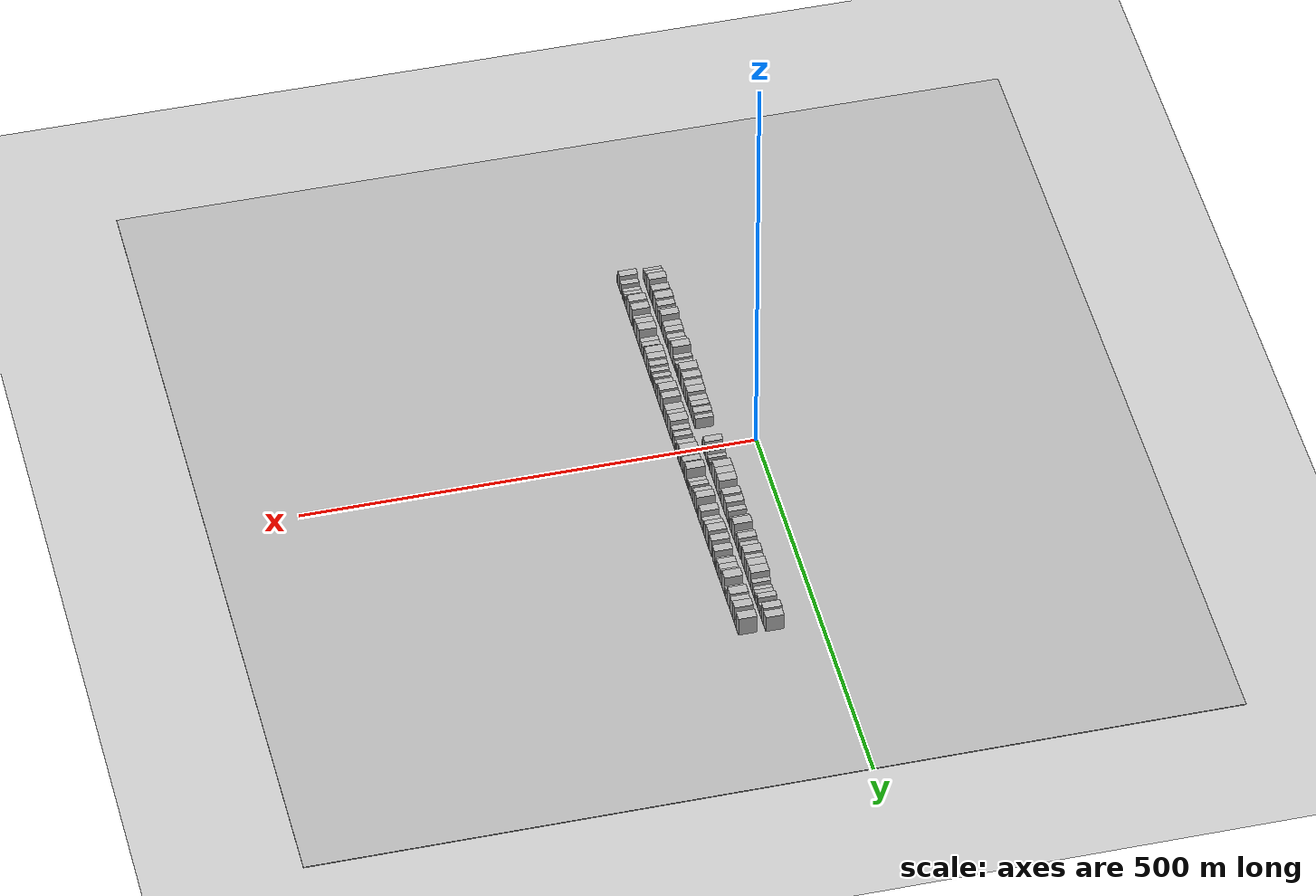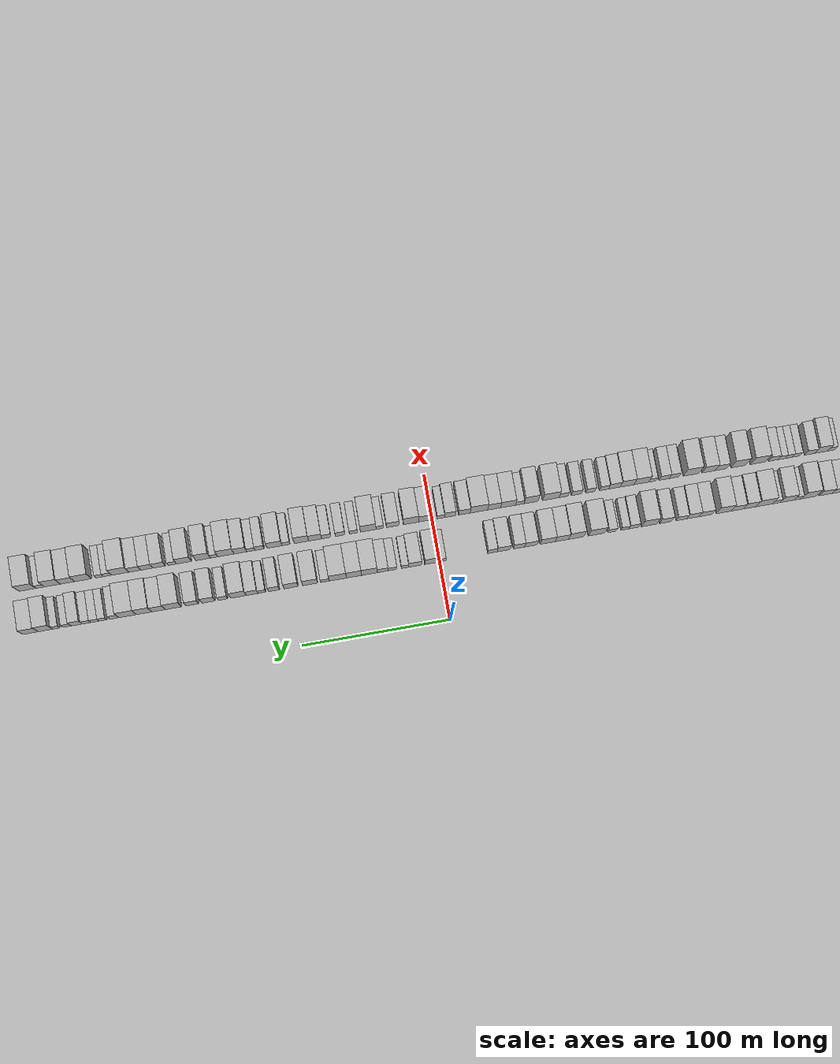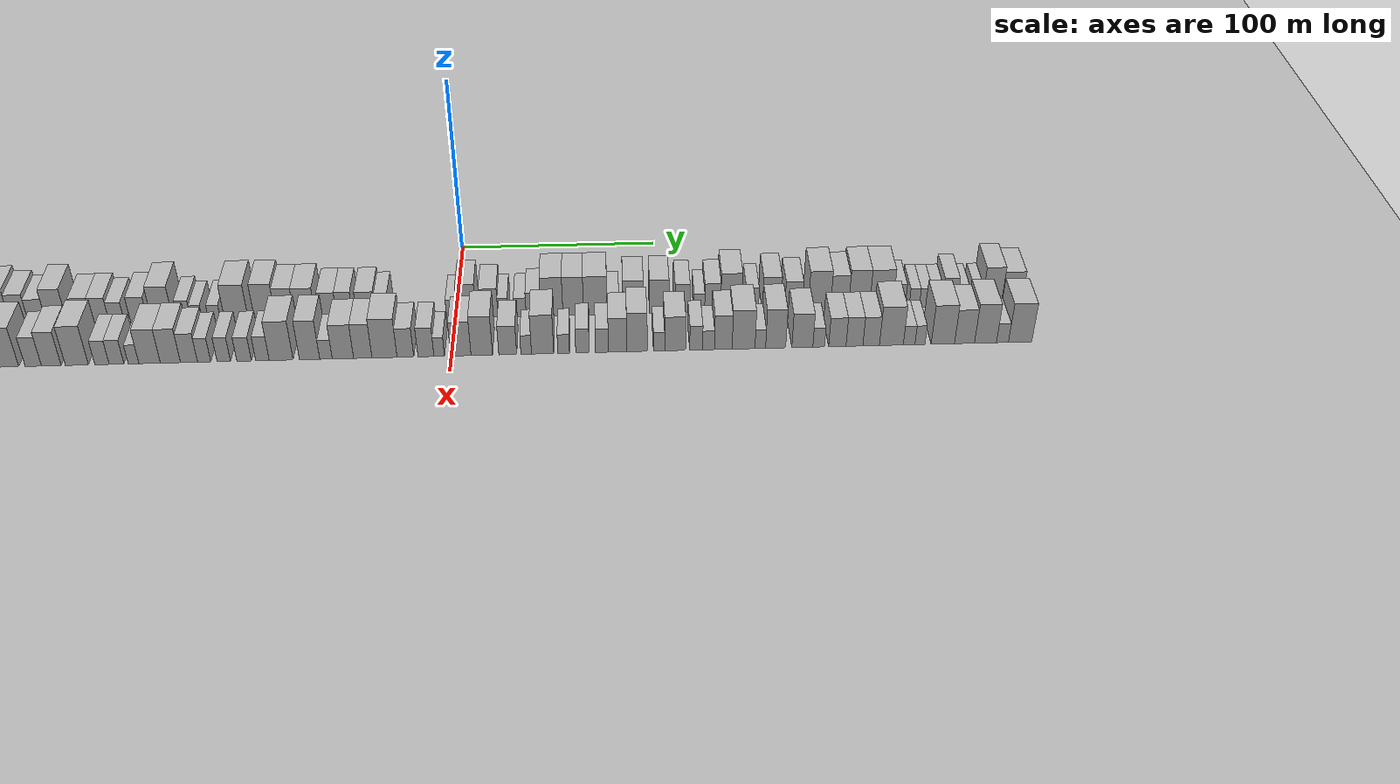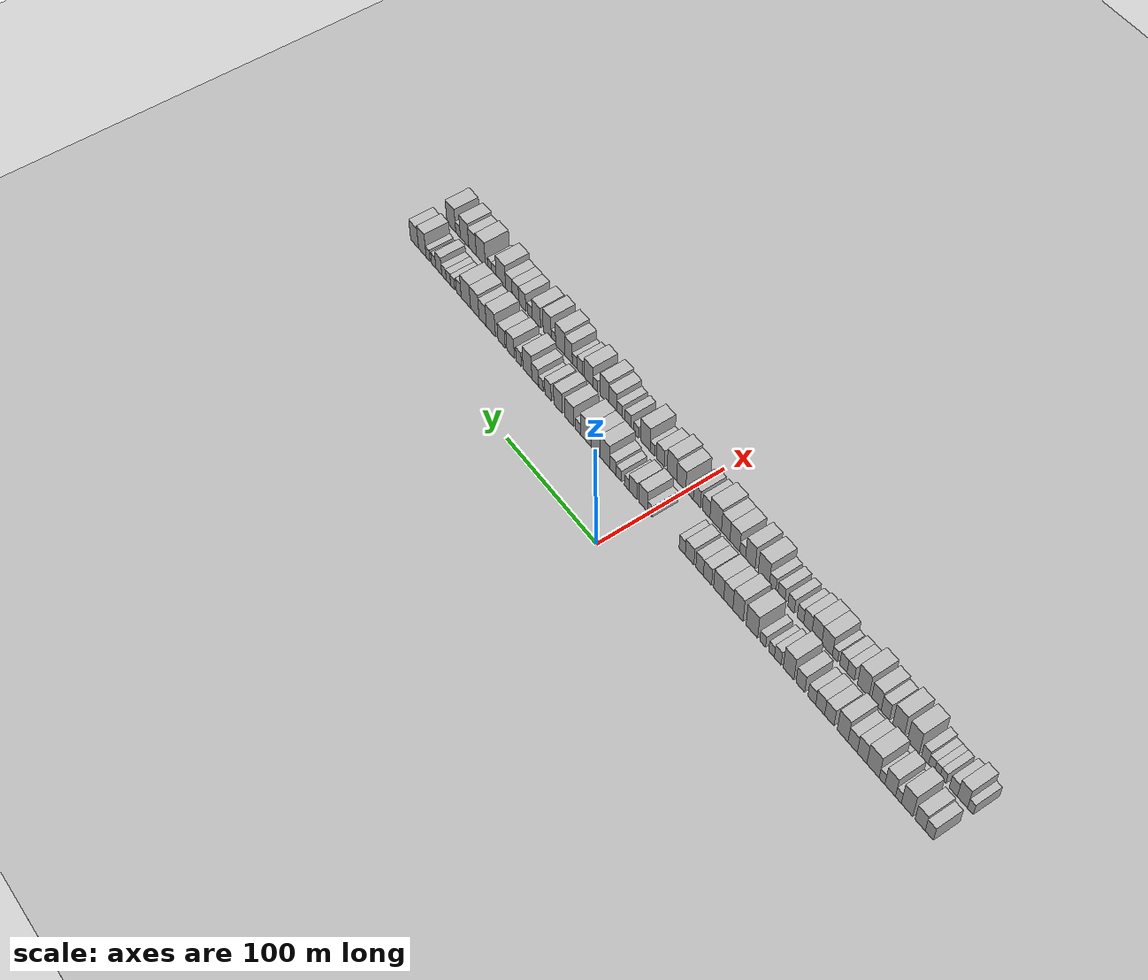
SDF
<?xml version="1.0" encoding="utf-8"?>

<sdf version="1.6">

   <world name="default">

      <gui fullscreen="0">

         <camera name="user_camera">

            <pose>-15 0 4.57585 0 0 0</pose>

            <view_controller>orbit</view_controller>

         </camera>

      </gui>

      <scene>

         <sky>

           <clouds>

             <speed>12</speed>

           </clouds>

         </sky>

         <ambient>0.4 0.4 0.4 1</ambient>

         <background>0.7 0.7 0.7 1</background>

         <shadows>1</shadows>

      </scene>

      <gravity>0 0 -9.8066</gravity>

      <magnetic_field>6e-06 2.3e-05 -4.2e-05</magnetic_field>

      <physics default="0" name="default_physics" type="ode">

         <ode>

            <solver>

               <type>quick</type>

               <iters>10</iters>

               <sor>1.0</sor>

               <use_dynamic_moi_rescaling>0</use_dynamic_moi_rescaling>

            </solver>

            <constraints>

               <cfm>0</cfm>

               <erp>0.2</erp>

               <contact_max_correcting_vel>100</contact_max_correcting_vel>

               <contact_surface_layer>0.001</contact_surface_layer>

            </constraints>

         </ode>

         <max_step_size>0.004</max_step_size>

         <real_time_factor>1</real_time_factor>

         <real_time_update_rate>250</real_time_update_rate>

      </physics>

      <light name="sun" type="directional">

         <cast_shadows>1</cast_shadows>

         <pose>0 0 10 0 0 0</pose>

         <diffuse>0.8 0.8 0.8 1</diffuse>

         <specular>0.2 0.2 0.2 1</specular>

         <attenuation>

            <range>1000</range>

            <constant>0.9</constant>

            <linear>0.01</linear>

            <quadratic>0.001</quadratic>

         </attenuation>

         <direction>-0.5 0.1 -0.9</direction>

      </light>

      <include>

         <name>ground_plane_1</name>

         <uri>model://HANNAS_ground_plane</uri>

         <pose>0 0 0  0 0 0</pose>

      </include>

      <include>

         <name>ground_plane_2</name>

         <uri>model://HANNAS_ground_plane</uri>

         <pose>100 0 0  0 0 0</pose>

      </include>

      <model name="building_1">

         <static>1</static>

         <pose frame="">50.0000 -271.3934 0 0.000000 0.000000 0.000000</pose>

         <link name="link">

            <pose frame="">0 0 7.50 0 0 0</pose>

            <collision name="collision">

               <geometry>

                  <box>

                     <size>20.0000 7.2133 15.0000</size>

                  </box>

               </geometry>

               <max_contacts>10</max_contacts>

               <surface>

                  <contact>

                     <ode/>

                  </contact>

                  <bounce/>

                  <friction>

                     <torsional>

                        <ode/>

                     </torsional>

                     <ode/>

                  </friction>

               </surface>

            </collision>

            <visual name="visual">

               <cast_shadows>0</cast_shadows>

               <geometry>

                  <box>

                     <size>20.0000 7.2133 15.0000</size>

                  </box>

               </geometry>

               <material>

                  <script>

                     <uri>model://HANNAS_wall/materials/scripts</uri>

                     <uri>model://HANNAS_wall/materials/textures</uri>

                     <name>vrc/HANNAS_wall</name>

                  </script>

               </material>

            </visual>

            <self_collide>0</self_collide>

            <enable_wind>0</enable_wind>

            <kinematic>0</kinematic>

         </link>

      </model>

      <model name="building_2">

         <static>1</static>

         <pose frame="">50.0000 -263.3516 0 0.000000 0.000000 0.000000</pose>

         <link name="link">

            <pose frame="">0 0 9.00 0 0 0</pose>

            <collision name="collision">

               <geometry>

                  <box>

                     <size>20.0000 8.8703 18.0000</size>

                  </box>

               </geometry>

               <max_contacts>10</max_contacts>

               <surface>

                  <contact>

                     <ode/>

                  </contact>

                  <bounce/>

                  <friction>

                     <torsional>

                        <ode/>

                     </torsional>

                     <ode/>

                  </friction>

               </surface>

            </collision>

            <visual name="visual">

               <cast_shadows>0</cast_shadows>

               <geometry>

                  <box>

                     <size>20.0000 8.8703 18.0000</size>

                  </box>

               </geometry>

               <material>

                  <script>

                     <uri>model://HANNAS_wall/materials/scripts</uri>

                     <uri>model://HANNAS_wall/materials/textures</uri>

                     <name>vrc/HANNAS_wall</name>

                  </script>

               </material>

            </visual>

            <self_collide>0</self_collide>

            <enable_wind>0</enable_wind>

            <kinematic>0</kinematic>

         </link>

      </model>

      <model name="building_3">

         <static>1</static>

         <pose frame="">50.0000 -251.8428 0 0.000000 0.000000 0.000000</pose>

         <link name="link">

            <pose frame="">0 0 12.00 0 0 0</pose>

            <collision name="collision">

               <geometry>

                  <box>

                     <size>20.0000 10.1471 24.0000</size>

                  </box>

               </geometry>

               <max_contacts>10</max_contacts>

               <surface>

                  <contact>

                     <ode/>

                  </contact>

                  <bounce/>

                  <friction>

                     <torsional>

                        <ode/>

                     </torsional>

                     <ode/>

                  </friction>

               </surface>

            </collision>

            <visual name="visual">

               <cast_shadows>0</cast_shadows>

               <geometry>

                  <box>

                     <size>20.0000 10.1471 24.0000</size>

                  </box>

               </geometry>

               <material>

                  <script>

                     <uri>model://HANNAS_wall/materials/scripts</uri>

                     <uri>model://HANNAS_wall/materials/textures</uri>

                     <name>vrc/HANNAS_wall</name>

                  </script>

               </material>

            </visual>

            <self_collide>0</self_collide>

            <enable_wind>0</enable_wind>

            <kinematic>0</kinematic>

         </link>

      </model>

      <model name="building_4">

         <static>1</static>

         <pose frame="">50.0000 -244.1770 0 0.000000 0.000000 0.000000</pose>

         <link name="link">

            <pose frame="">0 0 6.00 0 0 0</pose>

            <collision name="collision">

               <geometry>

                  <box>

                     <size>20.0000 5.1846 12.0000</size>

                  </box>

               </geometry>

               <max_contacts>10</max_contacts>

               <surface>

                  <contact>

                     <ode/>

                  </contact>

                  <bounce/>

                  <friction>

                     <torsional>

                        <ode/>

                     </torsional>

                     <ode/>

                  </friction>

               </surface>

            </collision>

            <visual name="visual">

               <cast_shadows>0</cast_shadows>

               <geometry>

                  <box>

                     <size>20.0000 5.1846 12.0000</size>

                  </box>

               </geometry>

               <material>

                  <script>

                     <uri>model://HANNAS_wall/materials/scripts</uri>

                     <uri>model://HANNAS_wall/materials/textures</uri>

                     <name>vrc/HANNAS_wall</name>

                  </script>

               </material>

            </visual>

            <self_collide>0</self_collide>

            <enable_wind>0</enable_wind>

            <kinematic>0</kinematic>

         </link>

      </model>

      <model name="building_5">

         <static>1</static>

         <pose frame="">50.0000 -236.8170 0 0.000000 0.000000 0.000000</pose>

         <link name="link">

            <pose frame="">0 0 10.50 0 0 0</pose>

            <collision name="collision">

               <geometry>

                  <box>

                     <size>20.0000 9.5352 21.0000</size>

                  </box>

               </geometry>

               <max_contacts>10</max_contacts>

               <surface>

                  <contact>

                     <ode/>

                  </contact>

                  <bounce/>

                  <friction>

                     <torsional>

                        <ode/>

                     </torsional>

                     <ode/>

                  </friction>

               </surface>

            </collision>

            <visual name="visual">

               <cast_shadows>0</cast_shadows>

               <geometry>

                  <box>

                     <size>20.0000 9.5352 21.0000</size>

                  </box>

               </geometry>

               <material>

                  <script>

                     <uri>model://HANNAS_wall/materials/scripts</uri>

                     <uri>model://HANNAS_wall/materials/textures</uri>

                     <name>vrc/HANNAS_wall</name>

                  </script>

               </material>

            </visual>

            <self_collide>0</self_collide>

            <enable_wind>0</enable_wind>

            <kinematic>0</kinematic>

         </link>

      </model>

      <model name="building_6">

         <static>1</static>

         <pose frame="">50.0000 -229.4893 0 0.000000 0.000000 0.000000</pose>

         <link name="link">

            <pose frame="">0 0 6.00 0 0 0</pose>

            <collision name="collision">

               <geometry>

                  <box>

                     <size>20.0000 5.1203 12.0000</size>

                  </box>

               </geometry>

               <max_contacts>10</max_contacts>

               <surface>

                  <contact>

                     <ode/>

                  </contact>

                  <bounce/>

                  <friction>

                     <torsional>

                        <ode/>

                     </torsional>

                     <ode/>

                  </friction>

               </surface>

            </collision>

            <visual name="visual">

               <cast_shadows>0</cast_shadows>

               <geometry>

                  <box>

                     <size>20.0000 5.1203 12.0000</size>

                  </box>

               </geometry>

               <material>

                  <script>

                     <uri>model://HANNAS_wall/materials/scripts</uri>

                     <uri>model://HANNAS_wall/materials/textures</uri>

                     <name>vrc/HANNAS_wall</name>

                  </script>

               </material>

            </visual>

            <self_collide>0</self_collide>

            <enable_wind>0</enable_wind>

            <kinematic>0</kinematic>

         </link>

      </model>

      <model name="building_7">

         <static>1</static>

         <pose frame="">50.0000 -221.3045 0 0.000000 0.000000 0.000000</pose>

         <link name="link">

            <pose frame="">0 0 12.00 0 0 0</pose>

            <collision name="collision">

               <geometry>

                  <box>

                     <size>20.0000 11.2494 24.0000</size>

                  </box>

               </geometry>

               <max_contacts>10</max_contacts>

               <surface>

                  <contact>

                     <ode/>

                  </contact>

                  <bounce/>

                  <friction>

                     <torsional>

                        <ode/>

                     </torsional>

                     <ode/>

                  </friction>

               </surface>

            </collision>

            <visual name="visual">

               <cast_shadows>0</cast_shadows>

               <geometry>

                  <box>

                     <size>20.0000 11.2494 24.0000</size>

                  </box>

               </geometry>

               <material>

                  <script>

                     <uri>model://HANNAS_wall/materials/scripts</uri>

                     <uri>model://HANNAS_wall/materials/textures</uri>

                     <name>vrc/HANNAS_wall</name>

                  </script>

               </material>

            </visual>

            <self_collide>0</self_collide>

            <enable_wind>0</enable_wind>

            <kinematic>0</kinematic>

         </link>

      </model>

      <model name="building_8">

         <static>1</static>

         <pose frame="">50.0000 -211.3098 0 0.000000 0.000000 0.000000</pose>

         <link name="link">

            <pose frame="">0 0 10.50 0 0 0</pose>

            <collision name="collision">

               <geometry>

                  <box>

                     <size>20.0000 8.7400 21.0000</size>

                  </box>

               </geometry>

               <max_contacts>10</max_contacts>

               <surface>

                  <contact>

                     <ode/>

                  </contact>

                  <bounce/>

                  <friction>

                     <torsional>

                        <ode/>

                     </torsional>

                     <ode/>

                  </friction>

               </surface>

            </collision>

            <visual name="visual">

               <cast_shadows>0</cast_shadows>

               <geometry>

                  <box>

                     <size>20.0000 8.7400 21.0000</size>

                  </box>

               </geometry>

               <material>

                  <script>

                     <uri>model://HANNAS_wall/materials/scripts</uri>

                     <uri>model://HANNAS_wall/materials/textures</uri>

                     <name>vrc/HANNAS_wall</name>

                  </script>

               </material>

            </visual>

            <self_collide>0</self_collide>

            <enable_wind>0</enable_wind>

            <kinematic>0</kinematic>

         </link>

      </model>

      <model name="building_9">

         <static>1</static>

         <pose frame="">50.0000 -202.6717 0 0.000000 0.000000 0.000000</pose>

         <link name="link">

            <pose frame="">0 0 9.00 0 0 0</pose>

            <collision name="collision">

               <geometry>

                  <box>

                     <size>20.0000 8.5363 18.0000</size>

                  </box>

               </geometry>

               <max_contacts>10</max_contacts>

               <surface>

                  <contact>

                     <ode/>

                  </contact>

                  <bounce/>

                  <friction>

                     <torsional>

                        <ode/>

                     </torsional>

                     <ode/>

                  </friction>

               </surface>

            </collision>

            <visual name="visual">

               <cast_shadows>0</cast_shadows>

               <geometry>

                  <box>

                     <size>20.0000 8.5363 18.0000</size>

                  </box>

               </geometry>

               <material>

                  <script>

                     <uri>model://HANNAS_wall/materials/scripts</uri>

                     <uri>model://HANNAS_wall/materials/textures</uri>

                     <name>vrc/HANNAS_wall</name>

                  </script>

               </material>

            </visual>

            <self_collide>0</self_collide>

            <enable_wind>0</enable_wind>

            <kinematic>0</kinematic>

         </link>

      </model>

      <model name="building_10">

         <static>1</static>

         <pose frame="">50.0000 -193.4217 0 0.000000 0.000000 0.000000</pose>

         <link name="link">

            <pose frame="">0 0 12.00 0 0 0</pose>

            <collision name="collision">

               <geometry>

                  <box>

                     <size>20.0000 9.9637 24.0000</size>

                  </box>

               </geometry>

               <max_contacts>10</max_contacts>

               <surface>

                  <contact>

                     <ode/>

                  </contact>

                  <bounce/>

                  <friction>

                     <torsional>

                        <ode/>

                     </torsional>

                     <ode/>

                  </friction>

               </surface>

            </collision>

            <visual name="visual">

               <cast_shadows>0</cast_shadows>

               <geometry>

                  <box>

                     <size>20.0000 9.9637 24.0000</size>

                  </box>

               </geometry>

               <material>

                  <script>

                     <uri>model://HANNAS_wall/materials/scripts</uri>

                     <uri>model://HANNAS_wall/materials/textures</uri>

                     <name>vrc/HANNAS_wall</name>

                  </script>

               </material>

            </visual>

            <self_collide>0</self_collide>

            <enable_wind>0</enable_wind>

            <kinematic>0</kinematic>

         </link>

      </model>

      <model name="building_11">

         <static>1</static>

         <pose frame="">50.0000 -181.0662 0 0.000000 0.000000 0.000000</pose>

         <link name="link">

            <pose frame="">0 0 9.00 0 0 0</pose>

            <collision name="collision">

               <geometry>

                  <box>

                     <size>20.0000 8.7472 18.0000</size>

                  </box>

               </geometry>

               <max_contacts>10</max_contacts>

               <surface>

                  <contact>

                     <ode/>

                  </contact>

                  <bounce/>

                  <friction>

                     <torsional>

                        <ode/>

                     </torsional>

                     <ode/>

                  </friction>

               </surface>

            </collision>

            <visual name="visual">

               <cast_shadows>0</cast_shadows>

               <geometry>

                  <box>

                     <size>20.0000 8.7472 18.0000</size>

                  </box>

               </geometry>

               <material>

                  <script>

                     <uri>model://HANNAS_wall/materials/scripts</uri>

                     <uri>model://HANNAS_wall/materials/textures</uri>

                     <name>vrc/HANNAS_wall</name>

                  </script>

               </material>

            </visual>

            <self_collide>0</self_collide>

            <enable_wind>0</enable_wind>

            <kinematic>0</kinematic>

         </link>

      </model>

      <model name="building_12">

         <static>1</static>

         <pose frame="">50.0000 -172.4583 0 0.000000 0.000000 0.000000</pose>

         <link name="link">

            <pose frame="">0 0 9.00 0 0 0</pose>

            <collision name="collision">

               <geometry>

                  <box>

                     <size>20.0000 8.4685 18.0000</size>

                  </box>

               </geometry>

               <max_contacts>10</max_contacts>

               <surface>

                  <contact>

                     <ode/>

                  </contact>

                  <bounce/>

                  <friction>

                     <torsional>

                        <ode/>

                     </torsional>

                     <ode/>

                  </friction>

               </surface>

            </collision>

            <visual name="visual">

               <cast_shadows>0</cast_shadows>

               <geometry>

                  <box>

                     <size>20.0000 8.4685 18.0000</size>

                  </box>

               </geometry>

               <material>

                  <script>

                     <uri>model://HANNAS_wall/materials/scripts</uri>

                     <uri>model://HANNAS_wall/materials/textures</uri>

                     <name>vrc/HANNAS_wall</name>

                  </script>

               </material>

            </visual>

            <self_collide>0</self_collide>

            <enable_wind>0</enable_wind>

            <kinematic>0</kinematic>

         </link>

      </model>

      <model name="building_13">

         <static>1</static>

         <pose frame="">50.0000 -164.5516 0 0.000000 0.000000 0.000000</pose>

         <link name="link">

            <pose frame="">0 0 7.50 0 0 0</pose>

            <collision name="collision">

               <geometry>

                  <box>

                     <size>20.0000 7.3451 15.0000</size>

                  </box>

               </geometry>

               <max_contacts>10</max_contacts>

               <surface>

                  <contact>

                     <ode/>

                  </contact>

                  <bounce/>

                  <friction>

                     <torsional>

                        <ode/>

                     </torsional>

                     <ode/>

                  </friction>

               </surface>

            </collision>

            <visual name="visual">

               <cast_shadows>0</cast_shadows>

               <geometry>

                  <box>

                     <size>20.0000 7.3451 15.0000</size>

                  </box>

               </geometry>

               <material>

                  <script>

                     <uri>model://HANNAS_wall/materials/scripts</uri>

                     <uri>model://HANNAS_wall/materials/textures</uri>

                     <name>vrc/HANNAS_wall</name>

                  </script>

               </material>

            </visual>

            <self_collide>0</self_collide>

            <enable_wind>0</enable_wind>

            <kinematic>0</kinematic>

         </link>

      </model>

      <model name="building_14">

         <static>1</static>

         <pose frame="">50.0000 -153.7193 0 0.000000 0.000000 0.000000</pose>

         <link name="link">

            <pose frame="">0 0 9.00 0 0 0</pose>

            <collision name="collision">

               <geometry>

                  <box>

                     <size>20.0000 8.3196 18.0000</size>

                  </box>

               </geometry>

               <max_contacts>10</max_contacts>

               <surface>

                  <contact>

                     <ode/>

                  </contact>

                  <bounce/>

                  <friction>

                     <torsional>

                        <ode/>

                     </torsional>

                     <ode/>

                  </friction>

               </surface>

            </collision>

            <visual name="visual">

               <cast_shadows>0</cast_shadows>

               <geometry>

                  <box>

                     <size>20.0000 8.3196 18.0000</size>

                  </box>

               </geometry>

               <material>

                  <script>

                     <uri>model://HANNAS_wall/materials/scripts</uri>

                     <uri>model://HANNAS_wall/materials/textures</uri>

                     <name>vrc/HANNAS_wall</name>

                  </script>

               </material>

            </visual>

            <self_collide>0</self_collide>

            <enable_wind>0</enable_wind>

            <kinematic>0</kinematic>

         </link>

      </model>

      <model name="building_15">

         <static>1</static>

         <pose frame="">50.0000 -142.3722 0 0.000000 0.000000 0.000000</pose>

         <link name="link">

            <pose frame="">0 0 12.00 0 0 0</pose>

            <collision name="collision">

               <geometry>

                  <box>

                     <size>20.0000 10.3744 24.0000</size>

                  </box>

               </geometry>

               <max_contacts>10</max_contacts>

               <surface>

                  <contact>

                     <ode/>

                  </contact>

                  <bounce/>

                  <friction>

                     <torsional>

                        <ode/>

                     </torsional>

                     <ode/>

                  </friction>

               </surface>

            </collision>

            <visual name="visual">

               <cast_shadows>0</cast_shadows>

               <geometry>

                  <box>

                     <size>20.0000 10.3744 24.0000</size>

                  </box>

               </geometry>

               <material>

                  <script>

                     <uri>model://HANNAS_wall/materials/scripts</uri>

                     <uri>model://HANNAS_wall/materials/textures</uri>

                     <name>vrc/HANNAS_wall</name>

                  </script>

               </material>

            </visual>

            <self_collide>0</self_collide>

            <enable_wind>0</enable_wind>

            <kinematic>0</kinematic>

         </link>

      </model>

      <model name="building_16">

         <static>1</static>

         <pose frame="">50.0000 -131.8775 0 0.000000 0.000000 0.000000</pose>

         <link name="link">

            <pose frame="">0 0 7.50 0 0 0</pose>

            <collision name="collision">

               <geometry>

                  <box>

                     <size>20.0000 6.6150 15.0000</size>

                  </box>

               </geometry>

               <max_contacts>10</max_contacts>

               <surface>

                  <contact>

                     <ode/>

                  </contact>

                  <bounce/>

                  <friction>

                     <torsional>

                        <ode/>

                     </torsional>

                     <ode/>

                  </friction>

               </surface>

            </collision>

            <visual name="visual">

               <cast_shadows>0</cast_shadows>

               <geometry>

                  <box>

                     <size>20.0000 6.6150 15.0000</size>

                  </box>

               </geometry>

               <material>

                  <script>

                     <uri>model://HANNAS_wall/materials/scripts</uri>

                     <uri>model://HANNAS_wall/materials/textures</uri>

                     <name>vrc/HANNAS_wall</name>

                  </script>

               </material>

            </visual>

            <self_collide>0</self_collide>

            <enable_wind>0</enable_wind>

            <kinematic>0</kinematic>

         </link>

      </model>

      <model name="building_17">

         <static>1</static>

         <pose frame="">50.0000 -125.8137 0 0.000000 0.000000 0.000000</pose>

         <link name="link">

            <pose frame="">0 0 6.00 0 0 0</pose>

            <collision name="collision">

               <geometry>

                  <box>

                     <size>20.0000 5.5126 12.0000</size>

                  </box>

               </geometry>

               <max_contacts>10</max_contacts>

               <surface>

                  <contact>

                     <ode/>

                  </contact>

                  <bounce/>

                  <friction>

                     <torsional>

                        <ode/>

                     </torsional>

                     <ode/>

                  </friction>

               </surface>

            </collision>

            <visual name="visual">

               <cast_shadows>0</cast_shadows>

               <geometry>

                  <box>

                     <size>20.0000 5.5126 12.0000</size>

                  </box>

               </geometry>

               <material>

                  <script>

                     <uri>model://HANNAS_wall/materials/scripts</uri>

                     <uri>model://HANNAS_wall/materials/textures</uri>

                     <name>vrc/HANNAS_wall</name>

                  </script>

               </material>

            </visual>

            <self_collide>0</self_collide>

            <enable_wind>0</enable_wind>

            <kinematic>0</kinematic>

         </link>

      </model>

      <model name="building_18">

         <static>1</static>

         <pose frame="">50.0000 -117.1598 0 0.000000 0.000000 0.000000</pose>

         <link name="link">

            <pose frame="">0 0 6.00 0 0 0</pose>

            <collision name="collision">

               <geometry>

                  <box>

                     <size>20.0000 5.7952 12.0000</size>

                  </box>

               </geometry>

               <max_contacts>10</max_contacts>

               <surface>

                  <contact>

                     <ode/>

                  </contact>

                  <bounce/>

                  <friction>

                     <torsional>

                        <ode/>

                     </torsional>

                     <ode/>

                  </friction>

               </surface>

            </collision>

            <visual name="visual">

               <cast_shadows>0</cast_shadows>

               <geometry>

                  <box>

                     <size>20.0000 5.7952 12.0000</size>

                  </box>

               </geometry>

               <material>

                  <script>

                     <uri>model://HANNAS_wall/materials/scripts</uri>

                     <uri>model://HANNAS_wall/materials/textures</uri>

                     <name>vrc/HANNAS_wall</name>

                  </script>

               </material>

            </visual>

            <self_collide>0</self_collide>

            <enable_wind>0</enable_wind>

            <kinematic>0</kinematic>

         </link>

      </model>

      <model name="building_19">

         <static>1</static>

         <pose frame="">50.0000 -106.5253 0 0.000000 0.000000 0.000000</pose>

         <link name="link">

            <pose frame="">0 0 12.00 0 0 0</pose>

            <collision name="collision">

               <geometry>

                  <box>

                     <size>20.0000 11.4739 24.0000</size>

                  </box>

               </geometry>

               <max_contacts>10</max_contacts>

               <surface>

                  <contact>

                     <ode/>

                  </contact>

                  <bounce/>

                  <friction>

                     <torsional>

                        <ode/>

                     </torsional>

                     <ode/>

                  </friction>

               </surface>

            </collision>

            <visual name="visual">

               <cast_shadows>0</cast_shadows>

               <geometry>

                  <box>

                     <size>20.0000 11.4739 24.0000</size>

                  </box>

               </geometry>

               <material>

                  <script>

                     <uri>model://HANNAS_wall/materials/scripts</uri>

                     <uri>model://HANNAS_wall/materials/textures</uri>

                     <name>vrc/HANNAS_wall</name>

                  </script>

               </material>

            </visual>

            <self_collide>0</self_collide>

            <enable_wind>0</enable_wind>

            <kinematic>0</kinematic>

         </link>

      </model>

      <model name="building_20">

         <static>1</static>

         <pose frame="">50.0000 -92.6263 0 0.000000 0.000000 0.000000</pose>

         <link name="link">

            <pose frame="">0 0 12.00 0 0 0</pose>

            <collision name="collision">

               <geometry>

                  <box>

                     <size>20.0000 10.3240 24.0000</size>

                  </box>

               </geometry>

               <max_contacts>10</max_contacts>

               <surface>

                  <contact>

                     <ode/>

                  </contact>

                  <bounce/>

                  <friction>

                     <torsional>

                        <ode/>

                     </torsional>

                     <ode/>

                  </friction>

               </surface>

            </collision>

            <visual name="visual">

               <cast_shadows>0</cast_shadows>

               <geometry>

                  <box>

                     <size>20.0000 10.3240 24.0000</size>

                  </box>

               </geometry>

               <material>

                  <script>

                     <uri>model://HANNAS_wall/materials/scripts</uri>

                     <uri>model://HANNAS_wall/materials/textures</uri>

                     <name>vrc/HANNAS_wall</name>

                  </script>

               </material>

            </visual>

            <self_collide>0</self_collide>

            <enable_wind>0</enable_wind>

            <kinematic>0</kinematic>

         </link>

      </model>

      <model name="building_21">

         <static>1</static>

         <pose frame="">50.0000 -82.8727 0 0.000000 0.000000 0.000000</pose>

         <link name="link">

            <pose frame="">0 0 10.50 0 0 0</pose>

            <collision name="collision">

               <geometry>

                  <box>

                     <size>20.0000 9.1832 21.0000</size>

                  </box>

               </geometry>

               <max_contacts>10</max_contacts>

               <surface>

                  <contact>

                     <ode/>

                  </contact>

                  <bounce/>

                  <friction>

                     <torsional>

                        <ode/>

                     </torsional>

                     <ode/>

                  </friction>

               </surface>

            </collision>

            <visual name="visual">

               <cast_shadows>0</cast_shadows>

               <geometry>

                  <box>

                     <size>20.0000 9.1832 21.0000</size>

                  </box>

               </geometry>

               <material>

                  <script>

                     <uri>model://HANNAS_wall/materials/scripts</uri>

                     <uri>model://HANNAS_wall/materials/textures</uri>

                     <name>vrc/HANNAS_wall</name>

                  </script>

               </material>

            </visual>

            <self_collide>0</self_collide>

            <enable_wind>0</enable_wind>

            <kinematic>0</kinematic>

         </link>

      </model>

      <model name="building_22">

         <static>1</static>

         <pose frame="">50.0000 -73.1384 0 0.000000 0.000000 0.000000</pose>

         <link name="link">

            <pose frame="">0 0 10.50 0 0 0</pose>

            <collision name="collision">

               <geometry>

                  <box>

                     <size>20.0000 10.2854 21.0000</size>

                  </box>

               </geometry>

               <max_contacts>10</max_contacts>

               <surface>

                  <contact>

                     <ode/>

                  </contact>

                  <bounce/>

                  <friction>

                     <torsional>

                        <ode/>

                     </torsional>

                     <ode/>

                  </friction>

               </surface>

            </collision>

            <visual name="visual">

               <cast_shadows>0</cast_shadows>

               <geometry>

                  <box>

                     <size>20.0000 10.2854 21.0000</size>

                  </box>

               </geometry>

               <material>

                  <script>

                     <uri>model://HANNAS_wall/materials/scripts</uri>

                     <uri>model://HANNAS_wall/materials/textures</uri>

                     <name>vrc/HANNAS_wall</name>

                  </script>

               </material>

            </visual>

            <self_collide>0</self_collide>

            <enable_wind>0</enable_wind>

            <kinematic>0</kinematic>

         </link>

      </model>

      <model name="building_23">

         <static>1</static>

         <pose frame="">50.0000 -61.7829 0 0.000000 0.000000 0.000000</pose>

         <link name="link">

            <pose frame="">0 0 9.00 0 0 0</pose>

            <collision name="collision">

               <geometry>

                  <box>

                     <size>20.0000 8.4257 18.0000</size>

                  </box>

               </geometry>

               <max_contacts>10</max_contacts>

               <surface>

                  <contact>

                     <ode/>

                  </contact>

                  <bounce/>

                  <friction>

                     <torsional>

                        <ode/>

                     </torsional>

                     <ode/>

                  </friction>

               </surface>

            </collision>

            <visual name="visual">

               <cast_shadows>0</cast_shadows>

               <geometry>

                  <box>

                     <size>20.0000 8.4257 18.0000</size>

                  </box>

               </geometry>

               <material>

                  <script>

                     <uri>model://HANNAS_wall/materials/scripts</uri>

                     <uri>model://HANNAS_wall/materials/textures</uri>

                     <name>vrc/HANNAS_wall</name>

                  </script>

               </material>

            </visual>

            <self_collide>0</self_collide>

            <enable_wind>0</enable_wind>

            <kinematic>0</kinematic>

         </link>

      </model>

      <model name="building_24">

         <static>1</static>

         <pose frame="">50.0000 -53.6768 0 0.000000 0.000000 0.000000</pose>

         <link name="link">

            <pose frame="">0 0 9.00 0 0 0</pose>

            <collision name="collision">

               <geometry>

                  <box>

                     <size>20.0000 7.7865 18.0000</size>

                  </box>

               </geometry>

               <max_contacts>10</max_contacts>

               <surface>

                  <contact>

                     <ode/>

                  </contact>

                  <bounce/>

                  <friction>

                     <torsional>

                        <ode/>

                     </torsional>

                     <ode/>

                  </friction>

               </surface>

            </collision>

            <visual name="visual">

               <cast_shadows>0</cast_shadows>

               <geometry>

                  <box>

                     <size>20.0000 7.7865 18.0000</size>

                  </box>

               </geometry>

               <material>

                  <script>

                     <uri>model://HANNAS_wall/materials/scripts</uri>

                     <uri>model://HANNAS_wall/materials/textures</uri>

                     <name>vrc/HANNAS_wall</name>

                  </script>

               </material>

            </visual>

            <self_collide>0</self_collide>

            <enable_wind>0</enable_wind>

            <kinematic>0</kinematic>

         </link>

      </model>

      <model name="building_25">

         <static>1</static>

         <pose frame="">50.0000 -43.2927 0 0.000000 0.000000 0.000000</pose>

         <link name="link">

            <pose frame="">0 0 9.00 0 0 0</pose>

            <collision name="collision">

               <geometry>

                  <box>

                     <size>20.0000 8.9817 18.0000</size>

                  </box>

               </geometry>

               <max_contacts>10</max_contacts>

               <surface>

                  <contact>

                     <ode/>

                  </contact>

                  <bounce/>

                  <friction>

                     <torsional>

                        <ode/>

                     </torsional>

                     <ode/>

                  </friction>

               </surface>

            </collision>

            <visual name="visual">

               <cast_shadows>0</cast_shadows>

               <geometry>

                  <box>

                     <size>20.0000 8.9817 18.0000</size>

                  </box>

               </geometry>

               <material>

                  <script>

                     <uri>model://HANNAS_wall/materials/scripts</uri>

                     <uri>model://HANNAS_wall/materials/textures</uri>

                     <name>vrc/HANNAS_wall</name>

                  </script>

               </material>

            </visual>

            <self_collide>0</self_collide>

            <enable_wind>0</enable_wind>

            <kinematic>0</kinematic>

         </link>

      </model>

      <model name="building_26">

         <static>1</static>

         <pose frame="">50.0000 -35.5720 0 0.000000 0.000000 0.000000</pose>

         <link name="link">

            <pose frame="">0 0 7.50 0 0 0</pose>

            <collision name="collision">

               <geometry>

                  <box>

                     <size>20.0000 6.4597 15.0000</size>

                  </box>

               </geometry>

               <max_contacts>10</max_contacts>

               <surface>

                  <contact>

                     <ode/>

                  </contact>

                  <bounce/>

                  <friction>

                     <torsional>

                        <ode/>

                     </torsional>

                     <ode/>

                  </friction>

               </surface>

            </collision>

            <visual name="visual">

               <cast_shadows>0</cast_shadows>

               <geometry>

                  <box>

                     <size>20.0000 6.4597 15.0000</size>

                  </box>

               </geometry>

               <material>

                  <script>

                     <uri>model://HANNAS_wall/materials/scripts</uri>

                     <uri>model://HANNAS_wall/materials/textures</uri>

                     <name>vrc/HANNAS_wall</name>

                  </script>

               </material>

            </visual>

            <self_collide>0</self_collide>

            <enable_wind>0</enable_wind>

            <kinematic>0</kinematic>

         </link>

      </model>

      <model name="building_27">

         <static>1</static>

         <pose frame="">50.0000 -1.3399 0 0.000000 0.000000 0.000000</pose>

         <link name="link">

            <pose frame="">0 0 6.00 0 0 0</pose>

            <collision name="collision">

               <geometry>

                  <box>

                     <size>20.0000 5.3348 12.0000</size>

                  </box>

               </geometry>

               <max_contacts>10</max_contacts>

               <surface>

                  <contact>

                     <ode/>

                  </contact>

                  <bounce/>

                  <friction>

                     <torsional>

                        <ode/>

                     </torsional>

                     <ode/>

                  </friction>

               </surface>

            </collision>

            <visual name="visual">

               <cast_shadows>0</cast_shadows>

               <geometry>

                  <box>

                     <size>20.0000 5.3348 12.0000</size>

                  </box>

               </geometry>

               <material>

                  <script>

                     <uri>model://HANNAS_wall/materials/scripts</uri>

                     <uri>model://HANNAS_wall/materials/textures</uri>

                     <name>vrc/HANNAS_wall</name>

                  </script>

               </material>

            </visual>

            <self_collide>0</self_collide>

            <enable_wind>0</enable_wind>

            <kinematic>0</kinematic>

         </link>

      </model>

      <model name="building_28">

         <static>1</static>

         <pose frame="">50.0000 5.8778 0 0.000000 0.000000 0.000000</pose>

         <link name="link">

            <pose frame="">0 0 10.50 0 0 0</pose>

            <collision name="collision">

               <geometry>

                  <box>

                     <size>20.0000 9.1007 21.0000</size>

                  </box>

               </geometry>

               <max_contacts>10</max_contacts>

               <surface>

                  <contact>

                     <ode/>

                  </contact>

                  <bounce/>

                  <friction>

                     <torsional>

                        <ode/>

                     </torsional>

                     <ode/>

                  </friction>

               </surface>

            </collision>

            <visual name="visual">

               <cast_shadows>0</cast_shadows>

               <geometry>

                  <box>

                     <size>20.0000 9.1007 21.0000</size>

                  </box>

               </geometry>

               <material>

                  <script>

                     <uri>model://HANNAS_wall/materials/scripts</uri>

                     <uri>model://HANNAS_wall/materials/textures</uri>

                     <name>vrc/HANNAS_wall</name>

                  </script>

               </material>

            </visual>

            <self_collide>0</self_collide>

            <enable_wind>0</enable_wind>

            <kinematic>0</kinematic>

         </link>

      </model>

      <model name="building_29">

         <static>1</static>

         <pose frame="">50.0000 16.8329 0 0.000000 0.000000 0.000000</pose>

         <link name="link">

            <pose frame="">0 0 9.00 0 0 0</pose>

            <collision name="collision">

               <geometry>

                  <box>

                     <size>20.0000 8.8094 18.0000</size>

                  </box>

               </geometry>

               <max_contacts>10</max_contacts>

               <surface>

                  <contact>

                     <ode/>

                  </contact>

                  <bounce/>

                  <friction>

                     <torsional>

                        <ode/>

                     </torsional>

                     <ode/>

                  </friction>

               </surface>

            </collision>

            <visual name="visual">

               <cast_shadows>0</cast_shadows>

               <geometry>

                  <box>

                     <size>20.0000 8.8094 18.0000</size>

                  </box>

               </geometry>

               <material>

                  <script>

                     <uri>model://HANNAS_wall/materials/scripts</uri>

                     <uri>model://HANNAS_wall/materials/textures</uri>

                     <name>vrc/HANNAS_wall</name>

                  </script>

               </material>

            </visual>

            <self_collide>0</self_collide>

            <enable_wind>0</enable_wind>

            <kinematic>0</kinematic>

         </link>

      </model>

      <model name="building_30">

         <static>1</static>

         <pose frame="">50.0000 23.7386 0 0.000000 0.000000 0.000000</pose>

         <link name="link">

            <pose frame="">0 0 6.00 0 0 0</pose>

            <collision name="collision">

               <geometry>

                  <box>

                     <size>20.0000 5.0021 12.0000</size>

                  </box>

               </geometry>

               <max_contacts>10</max_contacts>

               <surface>

                  <contact>

                     <ode/>

                  </contact>

                  <bounce/>

                  <friction>

                     <torsional>

                        <ode/>

                     </torsional>

                     <ode/>

                  </friction>

               </surface>

            </collision>

            <visual name="visual">

               <cast_shadows>0</cast_shadows>

               <geometry>

                  <box>

                     <size>20.0000 5.0021 12.0000</size>

                  </box>

               </geometry>

               <material>

                  <script>

                     <uri>model://HANNAS_wall/materials/scripts</uri>

                     <uri>model://HANNAS_wall/materials/textures</uri>

                     <name>vrc/HANNAS_wall</name>

                  </script>

               </material>

            </visual>

            <self_collide>0</self_collide>

            <enable_wind>0</enable_wind>

            <kinematic>0</kinematic>

         </link>

      </model>

      <model name="building_31">

         <static>1</static>

         <pose frame="">50.0000 32.1665 0 0.000000 0.000000 0.000000</pose>

         <link name="link">

            <pose frame="">0 0 6.00 0 0 0</pose>

            <collision name="collision">

               <geometry>

                  <box>

                     <size>20.0000 5.8538 12.0000</size>

                  </box>

               </geometry>

               <max_contacts>10</max_contacts>

               <surface>

                  <contact>

                     <ode/>

                  </contact>

                  <bounce/>

                  <friction>

                     <torsional>

                        <ode/>

                     </torsional>

                     <ode/>

                  </friction>

               </surface>

            </collision>

            <visual name="visual">

               <cast_shadows>0</cast_shadows>

               <geometry>

                  <box>

                     <size>20.0000 5.8538 12.0000</size>

                  </box>

               </geometry>

               <material>

                  <script>

                     <uri>model://HANNAS_wall/materials/scripts</uri>

                     <uri>model://HANNAS_wall/materials/textures</uri>

                     <name>vrc/HANNAS_wall</name>

                  </script>

               </material>

            </visual>

            <self_collide>0</self_collide>

            <enable_wind>0</enable_wind>

            <kinematic>0</kinematic>

         </link>

      </model>

      <model name="building_32">

         <static>1</static>

         <pose frame="">50.0000 38.7642 0 0.000000 0.000000 0.000000</pose>

         <link name="link">

            <pose frame="">0 0 7.50 0 0 0</pose>

            <collision name="collision">

               <geometry>

                  <box>

                     <size>20.0000 7.3415 15.0000</size>

                  </box>

               </geometry>

               <max_contacts>10</max_contacts>

               <surface>

                  <contact>

                     <ode/>

                  </contact>

                  <bounce/>

                  <friction>

                     <torsional>

                        <ode/>

                     </torsional>

                     <ode/>

                  </friction>

               </surface>

            </collision>

            <visual name="visual">

               <cast_shadows>0</cast_shadows>

               <geometry>

                  <box>

                     <size>20.0000 7.3415 15.0000</size>

                  </box>

               </geometry>

               <material>

                  <script>

                     <uri>model://HANNAS_wall/materials/scripts</uri>

                     <uri>model://HANNAS_wall/materials/textures</uri>

                     <name>vrc/HANNAS_wall</name>

                  </script>

               </material>

            </visual>

            <self_collide>0</self_collide>

            <enable_wind>0</enable_wind>

            <kinematic>0</kinematic>

         </link>

      </model>

      <model name="building_33">

         <static>1</static>

         <pose frame="">50.0000 47.8110 0 0.000000 0.000000 0.000000</pose>

         <link name="link">

            <pose frame="">0 0 12.00 0 0 0</pose>

            <collision name="collision">

               <geometry>

                  <box>

                     <size>20.0000 10.7521 24.0000</size>

                  </box>

               </geometry>

               <max_contacts>10</max_contacts>

               <surface>

                  <contact>

                     <ode/>

                  </contact>

                  <bounce/>

                  <friction>

                     <torsional>

                        <ode/>

                     </torsional>

                     <ode/>

                  </friction>

               </surface>

            </collision>

            <visual name="visual">

               <cast_shadows>0</cast_shadows>

               <geometry>

                  <box>

                     <size>20.0000 10.7521 24.0000</size>

                  </box>

               </geometry>

               <material>

                  <script>

                     <uri>model://HANNAS_wall/materials/scripts</uri>

                     <uri>model://HANNAS_wall/materials/textures</uri>

                     <name>vrc/HANNAS_wall</name>

                  </script>

               </material>

            </visual>

            <self_collide>0</self_collide>

            <enable_wind>0</enable_wind>

            <kinematic>0</kinematic>

         </link>

      </model>

      <model name="building_34">

         <static>1</static>

         <pose frame="">50.0000 58.2903 0 0.000000 0.000000 0.000000</pose>

         <link name="link">

            <pose frame="">0 0 12.00 0 0 0</pose>

            <collision name="collision">

               <geometry>

                  <box>

                     <size>20.0000 10.2065 24.0000</size>

                  </box>

               </geometry>

               <max_contacts>10</max_contacts>

               <surface>

                  <contact>

                     <ode/>

                  </contact>

                  <bounce/>

                  <friction>

                     <torsional>

                        <ode/>

                     </torsional>

                     <ode/>

                  </friction>

               </surface>

            </collision>

            <visual name="visual">

               <cast_shadows>0</cast_shadows>

               <geometry>

                  <box>

                     <size>20.0000 10.2065 24.0000</size>

                  </box>

               </geometry>

               <material>

                  <script>

                     <uri>model://HANNAS_wall/materials/scripts</uri>

                     <uri>model://HANNAS_wall/materials/textures</uri>

                     <name>vrc/HANNAS_wall</name>

                  </script>

               </material>

            </visual>

            <self_collide>0</self_collide>

            <enable_wind>0</enable_wind>

            <kinematic>0</kinematic>

         </link>

      </model>

      <model name="building_35">

         <static>1</static>

         <pose frame="">50.0000 69.1989 0 0.000000 0.000000 0.000000</pose>

         <link name="link">

            <pose frame="">0 0 12.00 0 0 0</pose>

            <collision name="collision">

               <geometry>

                  <box>

                     <size>20.0000 11.6106 24.0000</size>

                  </box>

               </geometry>

               <max_contacts>10</max_contacts>

               <surface>

                  <contact>

                     <ode/>

                  </contact>

                  <bounce/>

                  <friction>

                     <torsional>

                        <ode/>

                     </torsional>

                     <ode/>

                  </friction>

               </surface>

            </collision>

            <visual name="visual">

               <cast_shadows>0</cast_shadows>

               <geometry>

                  <box>

                     <size>20.0000 11.6106 24.0000</size>

                  </box>

               </geometry>

               <material>

                  <script>

                     <uri>model://HANNAS_wall/materials/scripts</uri>

                     <uri>model://HANNAS_wall/materials/textures</uri>

                     <name>vrc/HANNAS_wall</name>

                  </script>

               </material>

            </visual>

            <self_collide>0</self_collide>

            <enable_wind>0</enable_wind>

            <kinematic>0</kinematic>

         </link>

      </model>

      <model name="building_36">

         <static>1</static>

         <pose frame="">50.0000 77.9321 0 0.000000 0.000000 0.000000</pose>

         <link name="link">

            <pose frame="">0 0 6.00 0 0 0</pose>

            <collision name="collision">

               <geometry>

                  <box>

                     <size>20.0000 5.8558 12.0000</size>

                  </box>

               </geometry>

               <max_contacts>10</max_contacts>

               <surface>

                  <contact>

                     <ode/>

                  </contact>

                  <bounce/>

                  <friction>

                     <torsional>

                        <ode/>

                     </torsional>

                     <ode/>

                  </friction>

               </surface>

            </collision>

            <visual name="visual">

               <cast_shadows>0</cast_shadows>

               <geometry>

                  <box>

                     <size>20.0000 5.8558 12.0000</size>

                  </box>

               </geometry>

               <material>

                  <script>

                     <uri>model://HANNAS_wall/materials/scripts</uri>

                     <uri>model://HANNAS_wall/materials/textures</uri>

                     <name>vrc/HANNAS_wall</name>

                  </script>

               </material>

            </visual>

            <self_collide>0</self_collide>

            <enable_wind>0</enable_wind>

            <kinematic>0</kinematic>

         </link>

      </model>

      <model name="building_37">

         <static>1</static>

         <pose frame="">50.0000 87.9176 0 0.000000 0.000000 0.000000</pose>

         <link name="link">

            <pose frame="">0 0 10.50 0 0 0</pose>

            <collision name="collision">

               <geometry>

                  <box>

                     <size>20.0000 10.1152 21.0000</size>

                  </box>

               </geometry>

               <max_contacts>10</max_contacts>

               <surface>

                  <contact>

                     <ode/>

                  </contact>

                  <bounce/>

                  <friction>

                     <torsional>

                        <ode/>

                     </torsional>

                     <ode/>

                  </friction>

               </surface>

            </collision>

            <visual name="visual">

               <cast_shadows>0</cast_shadows>

               <geometry>

                  <box>

                     <size>20.0000 10.1152 21.0000</size>

                  </box>

               </geometry>

               <material>

                  <script>

                     <uri>model://HANNAS_wall/materials/scripts</uri>

                     <uri>model://HANNAS_wall/materials/textures</uri>

                     <name>vrc/HANNAS_wall</name>

                  </script>

               </material>

            </visual>

            <self_collide>0</self_collide>

            <enable_wind>0</enable_wind>

            <kinematic>0</kinematic>

         </link>

      </model>

      <model name="building_38">

         <static>1</static>

         <pose frame="">50.0000 100.7672 0 0.000000 0.000000 0.000000</pose>

         <link name="link">

            <pose frame="">0 0 10.50 0 0 0</pose>

            <collision name="collision">

               <geometry>

                  <box>

                     <size>20.0000 9.5838 21.0000</size>

                  </box>

               </geometry>

               <max_contacts>10</max_contacts>

               <surface>

                  <contact>

                     <ode/>

                  </contact>

                  <bounce/>

                  <friction>

                     <torsional>

                        <ode/>

                     </torsional>

                     <ode/>

                  </friction>

               </surface>

            </collision>

            <visual name="visual">

               <cast_shadows>0</cast_shadows>

               <geometry>

                  <box>

                     <size>20.0000 9.5838 21.0000</size>

                  </box>

               </geometry>

               <material>

                  <script>

                     <uri>model://HANNAS_wall/materials/scripts</uri>

                     <uri>model://HANNAS_wall/materials/textures</uri>

                     <name>vrc/HANNAS_wall</name>

                  </script>

               </material>

            </visual>

            <self_collide>0</self_collide>

            <enable_wind>0</enable_wind>

            <kinematic>0</kinematic>

         </link>

      </model>

      <model name="building_39">

         <static>1</static>

         <pose frame="">50.0000 112.2447 0 0.000000 0.000000 0.000000</pose>

         <link name="link">

            <pose frame="">0 0 9.00 0 0 0</pose>

            <collision name="collision">

               <geometry>

                  <box>

                     <size>20.0000 7.3713 18.0000</size>

                  </box>

               </geometry>

               <max_contacts>10</max_contacts>

               <surface>

                  <contact>

                     <ode/>

                  </contact>

                  <bounce/>

                  <friction>

                     <torsional>

                        <ode/>

                     </torsional>

                     <ode/>

                  </friction>

               </surface>

            </collision>

            <visual name="visual">

               <cast_shadows>0</cast_shadows>

               <geometry>

                  <box>

                     <size>20.0000 7.3713 18.0000</size>

                  </box>

               </geometry>

               <material>

                  <script>

                     <uri>model://HANNAS_wall/materials/scripts</uri>

                     <uri>model://HANNAS_wall/materials/textures</uri>

                     <name>vrc/HANNAS_wall</name>

                  </script>

               </material>

            </visual>

            <self_collide>0</self_collide>

            <enable_wind>0</enable_wind>

            <kinematic>0</kinematic>

         </link>

      </model>

      <model name="building_40">

         <static>1</static>

         <pose frame="">50.0000 120.5763 0 0.000000 0.000000 0.000000</pose>

         <link name="link">

            <pose frame="">0 0 6.00 0 0 0</pose>

            <collision name="collision">

               <geometry>

                  <box>

                     <size>20.0000 5.2918 12.0000</size>

                  </box>

               </geometry>

               <max_contacts>10</max_contacts>

               <surface>

                  <contact>

                     <ode/>

                  </contact>

                  <bounce/>

                  <friction>

                     <torsional>

                        <ode/>

                     </torsional>

                     <ode/>

                  </friction>

               </surface>

            </collision>

            <visual name="visual">

               <cast_shadows>0</cast_shadows>

               <geometry>

                  <box>

                     <size>20.0000 5.2918 12.0000</size>

                  </box>

               </geometry>

               <material>

                  <script>

                     <uri>model://HANNAS_wall/materials/scripts</uri>

                     <uri>model://HANNAS_wall/materials/textures</uri>

                     <name>vrc/HANNAS_wall</name>

                  </script>

               </material>

            </visual>

            <self_collide>0</self_collide>

            <enable_wind>0</enable_wind>

            <kinematic>0</kinematic>

         </link>

      </model>

      <model name="building_41">

         <static>1</static>

         <pose frame="">50.0000 127.1940 0 0.000000 0.000000 0.000000</pose>

         <link name="link">

            <pose frame="">0 0 9.00 0 0 0</pose>

            <collision name="collision">

               <geometry>

                  <box>

                     <size>20.0000 7.9437 18.0000</size>

                  </box>

               </geometry>

               <max_contacts>10</max_contacts>

               <surface>

                  <contact>

                     <ode/>

                  </contact>

                  <bounce/>

                  <friction>

                     <torsional>

                        <ode/>

                     </torsional>

                     <ode/>

                  </friction>

               </surface>

            </collision>

            <visual name="visual">

               <cast_shadows>0</cast_shadows>

               <geometry>

                  <box>

                     <size>20.0000 7.9437 18.0000</size>

                  </box>

               </geometry>

               <material>

                  <script>

                     <uri>model://HANNAS_wall/materials/scripts</uri>

                     <uri>model://HANNAS_wall/materials/textures</uri>

                     <name>vrc/HANNAS_wall</name>

                  </script>

               </material>

            </visual>

            <self_collide>0</self_collide>

            <enable_wind>0</enable_wind>

            <kinematic>0</kinematic>

         </link>

      </model>

      <model name="building_42">

         <static>1</static>

         <pose frame="">50.0000 136.3898 0 0.000000 0.000000 0.000000</pose>

         <link name="link">

            <pose frame="">0 0 12.00 0 0 0</pose>

            <collision name="collision">

               <geometry>

                  <box>

                     <size>20.0000 10.4479 24.0000</size>

                  </box>

               </geometry>

               <max_contacts>10</max_contacts>

               <surface>

                  <contact>

                     <ode/>

                  </contact>

                  <bounce/>

                  <friction>

                     <torsional>

                        <ode/>

                     </torsional>

                     <ode/>

                  </friction>

               </surface>

            </collision>

            <visual name="visual">

               <cast_shadows>0</cast_shadows>

               <geometry>

                  <box>

                     <size>20.0000 10.4479 24.0000</size>

                  </box>

               </geometry>

               <material>

                  <script>

                     <uri>model://HANNAS_wall/materials/scripts</uri>

                     <uri>model://HANNAS_wall/materials/textures</uri>

                     <name>vrc/HANNAS_wall</name>

                  </script>

               </material>

            </visual>

            <self_collide>0</self_collide>

            <enable_wind>0</enable_wind>

            <kinematic>0</kinematic>

         </link>

      </model>

      <model name="building_43">

         <static>1</static>

         <pose frame="">50.0000 146.7610 0 0.000000 0.000000 0.000000</pose>

         <link name="link">

            <pose frame="">0 0 7.50 0 0 0</pose>

            <collision name="collision">

               <geometry>

                  <box>

                     <size>20.0000 6.2945 15.0000</size>

                  </box>

               </geometry>

               <max_contacts>10</max_contacts>

               <surface>

                  <contact>

                     <ode/>

                  </contact>

                  <bounce/>

                  <friction>

                     <torsional>

                        <ode/>

                     </torsional>

                     <ode/>

                  </friction>

               </surface>

            </collision>

            <visual name="visual">

               <cast_shadows>0</cast_shadows>

               <geometry>

                  <box>

                     <size>20.0000 6.2945 15.0000</size>

                  </box>

               </geometry>

               <material>

                  <script>

                     <uri>model://HANNAS_wall/materials/scripts</uri>

                     <uri>model://HANNAS_wall/materials/textures</uri>

                     <name>vrc/HANNAS_wall</name>

                  </script>

               </material>

            </visual>

            <self_collide>0</self_collide>

            <enable_wind>0</enable_wind>

            <kinematic>0</kinematic>

         </link>

      </model>

      <model name="building_44">

         <static>1</static>

         <pose frame="">50.0000 156.4740 0 0.000000 0.000000 0.000000</pose>

         <link name="link">

            <pose frame="">0 0 10.50 0 0 0</pose>

            <collision name="collision">

               <geometry>

                  <box>

                     <size>20.0000 9.1314 21.0000</size>

                  </box>

               </geometry>

               <max_contacts>10</max_contacts>

               <surface>

                  <contact>

                     <ode/>

                  </contact>

                  <bounce/>

                  <friction>

                     <torsional>

                        <ode/>

                     </torsional>

                     <ode/>

                  </friction>

               </surface>

            </collision>

            <visual name="visual">

               <cast_shadows>0</cast_shadows>

               <geometry>

                  <box>

                     <size>20.0000 9.1314 21.0000</size>

                  </box>

               </geometry>

               <material>

                  <script>

                     <uri>model://HANNAS_wall/materials/scripts</uri>

                     <uri>model://HANNAS_wall/materials/textures</uri>

                     <name>vrc/HANNAS_wall</name>

                  </script>

               </material>

            </visual>

            <self_collide>0</self_collide>

            <enable_wind>0</enable_wind>

            <kinematic>0</kinematic>

         </link>

      </model>

      <model name="building_45">

         <static>1</static>

         <pose frame="">50.0000 167.3634 0 0.000000 0.000000 0.000000</pose>

         <link name="link">

            <pose frame="">0 0 9.00 0 0 0</pose>

            <collision name="collision">

               <geometry>

                  <box>

                     <size>20.0000 8.6474 18.0000</size>

                  </box>

               </geometry>

               <max_contacts>10</max_contacts>

               <surface>

                  <contact>

                     <ode/>

                  </contact>

                  <bounce/>

                  <friction>

                     <torsional>

                        <ode/>

                     </torsional>

                     <ode/>

                  </friction>

               </surface>

            </collision>

            <visual name="visual">

               <cast_shadows>0</cast_shadows>

               <geometry>

                  <box>

                     <size>20.0000 8.6474 18.0000</size>

                  </box>

               </geometry>

               <material>

                  <script>

                     <uri>model://HANNAS_wall/materials/scripts</uri>

                     <uri>model://HANNAS_wall/materials/textures</uri>

                     <name>vrc/HANNAS_wall</name>

                  </script>

               </material>

            </visual>

            <self_collide>0</self_collide>

            <enable_wind>0</enable_wind>

            <kinematic>0</kinematic>

         </link>

      </model>

      <model name="building_46">

         <static>1</static>

         <pose frame="">50.0000 180.2306 0 0.000000 0.000000 0.000000</pose>

         <link name="link">

            <pose frame="">0 0 12.00 0 0 0</pose>

            <collision name="collision">

               <geometry>

                  <box>

                     <size>20.0000 11.0870 24.0000</size>

                  </box>

               </geometry>

               <max_contacts>10</max_contacts>

               <surface>

                  <contact>

                     <ode/>

                  </contact>

                  <bounce/>

                  <friction>

                     <torsional>

                        <ode/>

                     </torsional>

                     <ode/>

                  </friction>

               </surface>

            </collision>

            <visual name="visual">

               <cast_shadows>0</cast_shadows>

               <geometry>

                  <box>

                     <size>20.0000 11.0870 24.0000</size>

                  </box>

               </geometry>

               <material>

                  <script>

                     <uri>model://HANNAS_wall/materials/scripts</uri>

                     <uri>model://HANNAS_wall/materials/textures</uri>

                     <name>vrc/HANNAS_wall</name>

                  </script>

               </material>

            </visual>

            <self_collide>0</self_collide>

            <enable_wind>0</enable_wind>

            <kinematic>0</kinematic>

         </link>

      </model>

      <model name="building_47">

         <static>1</static>

         <pose frame="">50.0000 190.2564 0 0.000000 0.000000 0.000000</pose>

         <link name="link">

            <pose frame="">0 0 10.50 0 0 0</pose>

            <collision name="collision">

               <geometry>

                  <box>

                     <size>20.0000 8.9645 21.0000</size>

                  </box>

               </geometry>

               <max_contacts>10</max_contacts>

               <surface>

                  <contact>

                     <ode/>

                  </contact>

                  <bounce/>

                  <friction>

                     <torsional>

                        <ode/>

                     </torsional>

                     <ode/>

                  </friction>

               </surface>

            </collision>

            <visual name="visual">

               <cast_shadows>0</cast_shadows>

               <geometry>

                  <box>

                     <size>20.0000 8.9645 21.0000</size>

                  </box>

               </geometry>

               <material>

                  <script>

                     <uri>model://HANNAS_wall/materials/scripts</uri>

                     <uri>model://HANNAS_wall/materials/textures</uri>

                     <name>vrc/HANNAS_wall</name>

                  </script>

               </material>

            </visual>

            <self_collide>0</self_collide>

            <enable_wind>0</enable_wind>

            <kinematic>0</kinematic>

         </link>

      </model>

      <model name="building_48">

         <static>1</static>

         <pose frame="">50.0000 199.9749 0 0.000000 0.000000 0.000000</pose>

         <link name="link">

            <pose frame="">0 0 12.00 0 0 0</pose>

            <collision name="collision">

               <geometry>

                  <box>

                     <size>20.0000 10.4727 24.0000</size>

                  </box>

               </geometry>

               <max_contacts>10</max_contacts>

               <surface>

                  <contact>

                     <ode/>

                  </contact>

                  <bounce/>

                  <friction>

                     <torsional>

                        <ode/>

                     </torsional>

                     <ode/>

                  </friction>

               </surface>

            </collision>

            <visual name="visual">

               <cast_shadows>0</cast_shadows>

               <geometry>

                  <box>

                     <size>20.0000 10.4727 24.0000</size>

                  </box>

               </geometry>

               <material>

                  <script>

                     <uri>model://HANNAS_wall/materials/scripts</uri>

                     <uri>model://HANNAS_wall/materials/textures</uri>

                     <name>vrc/HANNAS_wall</name>

                  </script>

               </material>

            </visual>

            <self_collide>0</self_collide>

            <enable_wind>0</enable_wind>

            <kinematic>0</kinematic>

         </link>

      </model>

      <model name="building_49">

         <static>1</static>

         <pose frame="">50.0000 211.0418 0 0.000000 0.000000 0.000000</pose>

         <link name="link">

            <pose frame="">0 0 12.00 0 0 0</pose>

            <collision name="collision">

               <geometry>

                  <box>

                     <size>20.0000 11.6610 24.0000</size>

                  </box>

               </geometry>

               <max_contacts>10</max_contacts>

               <surface>

                  <contact>

                     <ode/>

                  </contact>

                  <bounce/>

                  <friction>

                     <torsional>

                        <ode/>

                     </torsional>

                     <ode/>

                  </friction>

               </surface>

            </collision>

            <visual name="visual">

               <cast_shadows>0</cast_shadows>

               <geometry>

                  <box>

                     <size>20.0000 11.6610 24.0000</size>

                  </box>

               </geometry>

               <material>

                  <script>

                     <uri>model://HANNAS_wall/materials/scripts</uri>

                     <uri>model://HANNAS_wall/materials/textures</uri>

                     <name>vrc/HANNAS_wall</name>

                  </script>

               </material>

            </visual>

            <self_collide>0</self_collide>

            <enable_wind>0</enable_wind>

            <kinematic>0</kinematic>

         </link>

      </model>

      <model name="building_50">

         <static>1</static>

         <pose frame="">50.0000 219.9304 0 0.000000 0.000000 0.000000</pose>

         <link name="link">

            <pose frame="">0 0 7.50 0 0 0</pose>

            <collision name="collision">

               <geometry>

                  <box>

                     <size>20.0000 6.1162 15.0000</size>

                  </box>

               </geometry>

               <max_contacts>10</max_contacts>

               <surface>

                  <contact>

                     <ode/>

                  </contact>

                  <bounce/>

                  <friction>

                     <torsional>

                        <ode/>

                     </torsional>

                     <ode/>

                  </friction>

               </surface>

            </collision>

            <visual name="visual">

               <cast_shadows>0</cast_shadows>

               <geometry>

                  <box>

                     <size>20.0000 6.1162 15.0000</size>

                  </box>

               </geometry>

               <material>

                  <script>

                     <uri>model://HANNAS_wall/materials/scripts</uri>

                     <uri>model://HANNAS_wall/materials/textures</uri>

                     <name>vrc/HANNAS_wall</name>

                  </script>

               </material>

            </visual>

            <self_collide>0</self_collide>

            <enable_wind>0</enable_wind>

            <kinematic>0</kinematic>

         </link>

      </model>

      <model name="building_51">

         <static>1</static>

         <pose frame="">50.0000 227.5612 0 0.000000 0.000000 0.000000</pose>

         <link name="link">

            <pose frame="">0 0 6.00 0 0 0</pose>

            <collision name="collision">

               <geometry>

                  <box>

                     <size>20.0000 5.1453 12.0000</size>

                  </box>

               </geometry>

               <max_contacts>10</max_contacts>

               <surface>

                  <contact>

                     <ode/>

                  </contact>

                  <bounce/>

                  <friction>

                     <torsional>

                        <ode/>

                     </torsional>

                     <ode/>

                  </friction>

               </surface>

            </collision>

            <visual name="visual">

               <cast_shadows>0</cast_shadows>

               <geometry>

                  <box>

                     <size>20.0000 5.1453 12.0000</size>

                  </box>

               </geometry>

               <material>

                  <script>

                     <uri>model://HANNAS_wall/materials/scripts</uri>

                     <uri>model://HANNAS_wall/materials/textures</uri>

                     <name>vrc/HANNAS_wall</name>

                  </script>

               </material>

            </visual>

            <self_collide>0</self_collide>

            <enable_wind>0</enable_wind>

            <kinematic>0</kinematic>

         </link>

      </model>

      <model name="building_52">

         <static>1</static>

         <pose frame="">50.0000 232.9234 0 0.000000 0.000000 0.000000</pose>

         <link name="link">

            <pose frame="">0 0 6.00 0 0 0</pose>

            <collision name="collision">

               <geometry>

                  <box>

                     <size>20.0000 5.5791 12.0000</size>

                  </box>

               </geometry>

               <max_contacts>10</max_contacts>

               <surface>

                  <contact>

                     <ode/>

                  </contact>

                  <bounce/>

                  <friction>

                     <torsional>

                        <ode/>

                     </torsional>

                     <ode/>

                  </friction>

               </surface>

            </collision>

            <visual name="visual">

               <cast_shadows>0</cast_shadows>

               <geometry>

                  <box>

                     <size>20.0000 5.5791 12.0000</size>

                  </box>

               </geometry>

               <material>

                  <script>

                     <uri>model://HANNAS_wall/materials/scripts</uri>

                     <uri>model://HANNAS_wall/materials/textures</uri>

                     <name>vrc/HANNAS_wall</name>

                  </script>

               </material>

            </visual>

            <self_collide>0</self_collide>

            <enable_wind>0</enable_wind>

            <kinematic>0</kinematic>

         </link>

      </model>

      <model name="building_53">

         <static>1</static>

         <pose frame="">50.0000 238.5586 0 0.000000 0.000000 0.000000</pose>

         <link name="link">

            <pose frame="">0 0 6.00 0 0 0</pose>

            <collision name="collision">

               <geometry>

                  <box>

                     <size>20.0000 5.6915 12.0000</size>

                  </box>

               </geometry>

               <max_contacts>10</max_contacts>

               <surface>

                  <contact>

                     <ode/>

                  </contact>

                  <bounce/>

                  <friction>

                     <torsional>

                        <ode/>

                     </torsional>

                     <ode/>

                  </friction>

               </surface>

            </collision>

            <visual name="visual">

               <cast_shadows>0</cast_shadows>

               <geometry>

                  <box>

                     <size>20.0000 5.6915 12.0000</size>

                  </box>

               </geometry>

               <material>

                  <script>

                     <uri>model://HANNAS_wall/materials/scripts</uri>

                     <uri>model://HANNAS_wall/materials/textures</uri>

                     <name>vrc/HANNAS_wall</name>

                  </script>

               </material>

            </visual>

            <self_collide>0</self_collide>

            <enable_wind>0</enable_wind>

            <kinematic>0</kinematic>

         </link>

      </model>

      <model name="building_54">

         <static>1</static>

         <pose frame="">50.0000 245.1342 0 0.000000 0.000000 0.000000</pose>

         <link name="link">

            <pose frame="">0 0 9.00 0 0 0</pose>

            <collision name="collision">

               <geometry>

                  <box>

                     <size>20.0000 7.4597 18.0000</size>

                  </box>

               </geometry>

               <max_contacts>10</max_contacts>

               <surface>

                  <contact>

                     <ode/>

                  </contact>

                  <bounce/>

                  <friction>

                     <torsional>

                        <ode/>

                     </torsional>

                     <ode/>

                  </friction>

               </surface>

            </collision>

            <visual name="visual">

               <cast_shadows>0</cast_shadows>

               <geometry>

                  <box>

                     <size>20.0000 7.4597 18.0000</size>

                  </box>

               </geometry>

               <material>

                  <script>

                     <uri>model://HANNAS_wall/materials/scripts</uri>

                     <uri>model://HANNAS_wall/materials/textures</uri>

                     <name>vrc/HANNAS_wall</name>

                  </script>

               </material>

            </visual>

            <self_collide>0</self_collide>

            <enable_wind>0</enable_wind>

            <kinematic>0</kinematic>

         </link>

      </model>

      <model name="building_55">

         <static>1</static>

         <pose frame="">50.0000 251.6517 0 0.000000 0.000000 0.000000</pose>

         <link name="link">

            <pose frame="">0 0 6.00 0 0 0</pose>

            <collision name="collision">

               <geometry>

                  <box>

                     <size>20.0000 5.5754 12.0000</size>

                  </box>

               </geometry>

               <max_contacts>10</max_contacts>

               <surface>

                  <contact>

                     <ode/>

                  </contact>

                  <bounce/>

                  <friction>

                     <torsional>

                        <ode/>

                     </torsional>

                     <ode/>

                  </friction>

               </surface>

            </collision>

            <visual name="visual">

               <cast_shadows>0</cast_shadows>

               <geometry>

                  <box>

                     <size>20.0000 5.5754 12.0000</size>

                  </box>

               </geometry>

               <material>

                  <script>

                     <uri>model://HANNAS_wall/materials/scripts</uri>

                     <uri>model://HANNAS_wall/materials/textures</uri>

                     <name>vrc/HANNAS_wall</name>

                  </script>

               </material>

            </visual>

            <self_collide>0</self_collide>

            <enable_wind>0</enable_wind>

            <kinematic>0</kinematic>

         </link>

      </model>

      <model name="building_56">

         <static>1</static>

         <pose frame="">50.0000 258.8911 0 0.000000 0.000000 0.000000</pose>

         <link name="link">

            <pose frame="">0 0 6.00 0 0 0</pose>

            <collision name="collision">

               <geometry>

                  <box>

                     <size>20.0000 4.9034 12.0000</size>

                  </box>

               </geometry>

               <max_contacts>10</max_contacts>

               <surface>

                  <contact>

                     <ode/>

                  </contact>

                  <bounce/>

                  <friction>

                     <torsional>

                        <ode/>

                     </torsional>

                     <ode/>

                  </friction>

               </surface>

            </collision>

            <visual name="visual">

               <cast_shadows>0</cast_shadows>

               <geometry>

                  <box>

                     <size>20.0000 4.9034 12.0000</size>

                  </box>

               </geometry>

               <material>

                  <script>

                     <uri>model://HANNAS_wall/materials/scripts</uri>

                     <uri>model://HANNAS_wall/materials/textures</uri>

                     <name>vrc/HANNAS_wall</name>

                  </script>

               </material>

            </visual>

            <self_collide>0</self_collide>

            <enable_wind>0</enable_wind>

            <kinematic>0</kinematic>

         </link>

      </model>

      <model name="building_57">

         <static>1</static>

         <pose frame="">50.0000 266.1980 0 0.000000 0.000000 0.000000</pose>

         <link name="link">

            <pose frame="">0 0 12.00 0 0 0</pose>

            <collision name="collision">

               <geometry>

                  <box>

                     <size>20.0000 9.7103 24.0000</size>

                  </box>

               </geometry>

               <max_contacts>10</max_contacts>

               <surface>

                  <contact>

                     <ode/>

                  </contact>

                  <bounce/>

                  <friction>

                     <torsional>

                        <ode/>

                     </torsional>

                     <ode/>

                  </friction>

               </surface>

            </collision>

            <visual name="visual">

               <cast_shadows>0</cast_shadows>

               <geometry>

                  <box>

                     <size>20.0000 9.7103 24.0000</size>

                  </box>

               </geometry>

               <material>

                  <script>

                     <uri>model://HANNAS_wall/materials/scripts</uri>

                     <uri>model://HANNAS_wall/materials/textures</uri>

                     <name>vrc/HANNAS_wall</name>

                  </script>

               </material>

            </visual>

            <self_collide>0</self_collide>

            <enable_wind>0</enable_wind>

            <kinematic>0</kinematic>

         </link>

      </model>

      <model name="building_58">

         <static>1</static>

         <pose frame="">50.0000 276.2072 0 0.000000 0.000000 0.000000</pose>

         <link name="link">

            <pose frame="">0 0 10.50 0 0 0</pose>

            <collision name="collision">

               <geometry>

                  <box>

                     <size>20.0000 10.3082 21.0000</size>

                  </box>

               </geometry>

               <max_contacts>10</max_contacts>

               <surface>

                  <contact>

                     <ode/>

                  </contact>

                  <bounce/>

                  <friction>

                     <torsional>

                        <ode/>

                     </torsional>

                     <ode/>

                  </friction>

               </surface>

            </collision>

            <visual name="visual">

               <cast_shadows>0</cast_shadows>

               <geometry>

                  <box>

                     <size>20.0000 10.3082 21.0000</size>

                  </box>

               </geometry>

               <material>

                  <script>

                     <uri>model://HANNAS_wall/materials/scripts</uri>

                     <uri>model://HANNAS_wall/materials/textures</uri>

                     <name>vrc/HANNAS_wall</name>

                  </script>

               </material>

            </visual>

            <self_collide>0</self_collide>

            <enable_wind>0</enable_wind>

            <kinematic>0</kinematic>

         </link>

      </model>

      <model name="building_59">

         <static>1</static>

         <pose frame="">79.0000 -273.4948 0 0.000000 0.000000 0.000000</pose>

         <link name="link">

            <pose frame="">0 0 6.00 0 0 0</pose>

            <collision name="collision">

               <geometry>

                  <box>

                     <size>20.0000 5.0103 12.0000</size>

                  </box>

               </geometry>

               <max_contacts>10</max_contacts>

               <surface>

                  <contact>

                     <ode/>

                  </contact>

                  <bounce/>

                  <friction>

                     <torsional>

                        <ode/>

                     </torsional>

                     <ode/>

                  </friction>

               </surface>

            </collision>

            <visual name="visual">

               <cast_shadows>0</cast_shadows>

               <geometry>

                  <box>

                     <size>20.0000 5.0103 12.0000</size>

                  </box>

               </geometry>

               <material>

                  <script>

                     <uri>model://HANNAS_wall/materials/scripts</uri>

                     <uri>model://HANNAS_wall/materials/textures</uri>

                     <name>vrc/HANNAS_wall</name>

                  </script>

               </material>

            </visual>

            <self_collide>0</self_collide>

            <enable_wind>0</enable_wind>

            <kinematic>0</kinematic>

         </link>

      </model>

      <model name="building_60">

         <static>1</static>

         <pose frame="">79.0000 -266.5489 0 0.000000 0.000000 0.000000</pose>

         <link name="link">

            <pose frame="">0 0 10.50 0 0 0</pose>

            <collision name="collision">

               <geometry>

                  <box>

                     <size>20.0000 8.8815 21.0000</size>

                  </box>

               </geometry>

               <max_contacts>10</max_contacts>

               <surface>

                  <contact>

                     <ode/>

                  </contact>

                  <bounce/>

                  <friction>

                     <torsional>

                        <ode/>

                     </torsional>

                     <ode/>

                  </friction>

               </surface>

            </collision>

            <visual name="visual">

               <cast_shadows>0</cast_shadows>

               <geometry>

                  <box>

                     <size>20.0000 8.8815 21.0000</size>

                  </box>

               </geometry>

               <material>

                  <script>

                     <uri>model://HANNAS_wall/materials/scripts</uri>

                     <uri>model://HANNAS_wall/materials/textures</uri>

                     <name>vrc/HANNAS_wall</name>

                  </script>

               </material>

            </visual>

            <self_collide>0</self_collide>

            <enable_wind>0</enable_wind>

            <kinematic>0</kinematic>

         </link>

      </model>

      <model name="building_61">

         <static>1</static>

         <pose frame="">79.0000 -258.5615 0 0.000000 0.000000 0.000000</pose>

         <link name="link">

            <pose frame="">0 0 7.50 0 0 0</pose>

            <collision name="collision">

               <geometry>

                  <box>

                     <size>20.0000 7.0934 15.0000</size>

                  </box>

               </geometry>

               <max_contacts>10</max_contacts>

               <surface>

                  <contact>

                     <ode/>

                  </contact>

                  <bounce/>

                  <friction>

                     <torsional>

                        <ode/>

                     </torsional>

                     <ode/>

                  </friction>

               </surface>

            </collision>

            <visual name="visual">

               <cast_shadows>0</cast_shadows>

               <geometry>

                  <box>

                     <size>20.0000 7.0934 15.0000</size>

                  </box>

               </geometry>

               <material>

                  <script>

                     <uri>model://HANNAS_wall/materials/scripts</uri>

                     <uri>model://HANNAS_wall/materials/textures</uri>

                     <name>vrc/HANNAS_wall</name>

                  </script>

               </material>

            </visual>

            <self_collide>0</self_collide>

            <enable_wind>0</enable_wind>

            <kinematic>0</kinematic>

         </link>

      </model>

      <model name="building_62">

         <static>1</static>

         <pose frame="">79.0000 -249.4196 0 0.000000 0.000000 0.000000</pose>

         <link name="link">

            <pose frame="">0 0 6.00 0 0 0</pose>

            <collision name="collision">

               <geometry>

                  <box>

                     <size>20.0000 5.1904 12.0000</size>

                  </box>

               </geometry>

               <max_contacts>10</max_contacts>

               <surface>

                  <contact>

                     <ode/>

                  </contact>

                  <bounce/>

                  <friction>

                     <torsional>

                        <ode/>

                     </torsional>

                     <ode/>

                  </friction>

               </surface>

            </collision>

            <visual name="visual">

               <cast_shadows>0</cast_shadows>

               <geometry>

                  <box>

                     <size>20.0000 5.1904 12.0000</size>

                  </box>

               </geometry>

               <material>

                  <script>

                     <uri>model://HANNAS_wall/materials/scripts</uri>

                     <uri>model://HANNAS_wall/materials/textures</uri>

                     <name>vrc/HANNAS_wall</name>

                  </script>

               </material>

            </visual>

            <self_collide>0</self_collide>

            <enable_wind>0</enable_wind>

            <kinematic>0</kinematic>

         </link>

      </model>

      <model name="building_63">

         <static>1</static>

         <pose frame="">79.0000 -244.3865 0 0.000000 0.000000 0.000000</pose>

         <link name="link">

            <pose frame="">0 0 6.00 0 0 0</pose>

            <collision name="collision">

               <geometry>

                  <box>

                     <size>20.0000 4.8758 12.0000</size>

                  </box>

               </geometry>

               <max_contacts>10</max_contacts>

               <surface>

                  <contact>

                     <ode/>

                  </contact>

                  <bounce/>

                  <friction>

                     <torsional>

                        <ode/>

                     </torsional>

                     <ode/>

                  </friction>

               </surface>

            </collision>

            <visual name="visual">

               <cast_shadows>0</cast_shadows>

               <geometry>

                  <box>

                     <size>20.0000 4.8758 12.0000</size>

                  </box>

               </geometry>

               <material>

                  <script>

                     <uri>model://HANNAS_wall/materials/scripts</uri>

                     <uri>model://HANNAS_wall/materials/textures</uri>

                     <name>vrc/HANNAS_wall</name>

                  </script>

               </material>

            </visual>

            <self_collide>0</self_collide>

            <enable_wind>0</enable_wind>

            <kinematic>0</kinematic>

         </link>

      </model>

      <model name="building_64">

         <static>1</static>

         <pose frame="">79.0000 -239.3299 0 0.000000 0.000000 0.000000</pose>

         <link name="link">

            <pose frame="">0 0 6.00 0 0 0</pose>

            <collision name="collision">

               <geometry>

                  <box>

                     <size>20.0000 5.2375 12.0000</size>

                  </box>

               </geometry>

               <max_contacts>10</max_contacts>

               <surface>

                  <contact>

                     <ode/>

                  </contact>

                  <bounce/>

                  <friction>

                     <torsional>

                        <ode/>

                     </torsional>

                     <ode/>

                  </friction>

               </surface>

            </collision>

            <visual name="visual">

               <cast_shadows>0</cast_shadows>

               <geometry>

                  <box>

                     <size>20.0000 5.2375 12.0000</size>

                  </box>

               </geometry>

               <material>

                  <script>

                     <uri>model://HANNAS_wall/materials/scripts</uri>

                     <uri>model://HANNAS_wall/materials/textures</uri>

                     <name>vrc/HANNAS_wall</name>

                  </script>

               </material>

            </visual>

            <self_collide>0</self_collide>

            <enable_wind>0</enable_wind>

            <kinematic>0</kinematic>

         </link>

      </model>

      <model name="building_65">

         <static>1</static>

         <pose frame="">79.0000 -233.5546 0 0.000000 0.000000 0.000000</pose>

         <link name="link">

            <pose frame="">0 0 7.50 0 0 0</pose>

            <collision name="collision">

               <geometry>

                  <box>

                     <size>20.0000 6.3130 15.0000</size>

                  </box>

               </geometry>

               <max_contacts>10</max_contacts>

               <surface>

                  <contact>

                     <ode/>

                  </contact>

                  <bounce/>

                  <friction>

                     <torsional>

                        <ode/>

                     </torsional>

                     <ode/>

                  </friction>

               </surface>

            </collision>

            <visual name="visual">

               <cast_shadows>0</cast_shadows>

               <geometry>

                  <box>

                     <size>20.0000 6.3130 15.0000</size>

                  </box>

               </geometry>

               <material>

                  <script>

                     <uri>model://HANNAS_wall/materials/scripts</uri>

                     <uri>model://HANNAS_wall/materials/textures</uri>

                     <name>vrc/HANNAS_wall</name>

                  </script>

               </material>

            </visual>

            <self_collide>0</self_collide>

            <enable_wind>0</enable_wind>

            <kinematic>0</kinematic>

         </link>

      </model>

      <model name="building_66">

         <static>1</static>

         <pose frame="">79.0000 -223.0500 0 0.000000 0.000000 0.000000</pose>

         <link name="link">

            <pose frame="">0 0 12.00 0 0 0</pose>

            <collision name="collision">

               <geometry>

                  <box>

                     <size>20.0000 10.6962 24.0000</size>

                  </box>

               </geometry>

               <max_contacts>10</max_contacts>

               <surface>

                  <contact>

                     <ode/>

                  </contact>

                  <bounce/>

                  <friction>

                     <torsional>

                        <ode/>

                     </torsional>

                     <ode/>

                  </friction>

               </surface>

            </collision>

            <visual name="visual">

               <cast_shadows>0</cast_shadows>

               <geometry>

                  <box>

                     <size>20.0000 10.6962 24.0000</size>

                  </box>

               </geometry>

               <material>

                  <script>

                     <uri>model://HANNAS_wall/materials/scripts</uri>

                     <uri>model://HANNAS_wall/materials/textures</uri>

                     <name>vrc/HANNAS_wall</name>

                  </script>

               </material>

            </visual>

            <self_collide>0</self_collide>

            <enable_wind>0</enable_wind>

            <kinematic>0</kinematic>

         </link>

      </model>

      <model name="building_67">

         <static>1</static>

         <pose frame="">79.0000 -209.5441 0 0.000000 0.000000 0.000000</pose>

         <link name="link">

            <pose frame="">0 0 12.00 0 0 0</pose>

            <collision name="collision">

               <geometry>

                  <box>

                     <size>20.0000 10.3157 24.0000</size>

                  </box>

               </geometry>

               <max_contacts>10</max_contacts>

               <surface>

                  <contact>

                     <ode/>

                  </contact>

                  <bounce/>

                  <friction>

                     <torsional>

                        <ode/>

                     </torsional>

                     <ode/>

                  </friction>

               </surface>

            </collision>

            <visual name="visual">

               <cast_shadows>0</cast_shadows>

               <geometry>

                  <box>

                     <size>20.0000 10.3157 24.0000</size>

                  </box>

               </geometry>

               <material>

                  <script>

                     <uri>model://HANNAS_wall/materials/scripts</uri>

                     <uri>model://HANNAS_wall/materials/textures</uri>

                     <name>vrc/HANNAS_wall</name>

                  </script>

               </material>

            </visual>

            <self_collide>0</self_collide>

            <enable_wind>0</enable_wind>

            <kinematic>0</kinematic>

         </link>

      </model>

      <model name="building_68">

         <static>1</static>

         <pose frame="">79.0000 -197.5531 0 0.000000 0.000000 0.000000</pose>

         <link name="link">

            <pose frame="">0 0 9.00 0 0 0</pose>

            <collision name="collision">

               <geometry>

                  <box>

                     <size>20.0000 7.6663 18.0000</size>

                  </box>

               </geometry>

               <max_contacts>10</max_contacts>

               <surface>

                  <contact>

                     <ode/>

                  </contact>

                  <bounce/>

                  <friction>

                     <torsional>

                        <ode/>

                     </torsional>

                     <ode/>

                  </friction>

               </surface>

            </collision>

            <visual name="visual">

               <cast_shadows>0</cast_shadows>

               <geometry>

                  <box>

                     <size>20.0000 7.6663 18.0000</size>

                  </box>

               </geometry>

               <material>

                  <script>

                     <uri>model://HANNAS_wall/materials/scripts</uri>

                     <uri>model://HANNAS_wall/materials/textures</uri>

                     <name>vrc/HANNAS_wall</name>

                  </script>

               </material>

            </visual>

            <self_collide>0</self_collide>

            <enable_wind>0</enable_wind>

            <kinematic>0</kinematic>

         </link>

      </model>

      <model name="building_69">

         <static>1</static>

         <pose frame="">79.0000 -189.1175 0 0.000000 0.000000 0.000000</pose>

         <link name="link">

            <pose frame="">0 0 10.50 0 0 0</pose>

            <collision name="collision">

               <geometry>

                  <box>

                     <size>20.0000 9.2048 21.0000</size>

                  </box>

               </geometry>

               <max_contacts>10</max_contacts>

               <surface>

                  <contact>

                     <ode/>

                  </contact>

                  <bounce/>

                  <friction>

                     <torsional>

                        <ode/>

                     </torsional>

                     <ode/>

                  </friction>

               </surface>

            </collision>

            <visual name="visual">

               <cast_shadows>0</cast_shadows>

               <geometry>

                  <box>

                     <size>20.0000 9.2048 21.0000</size>

                  </box>

               </geometry>

               <material>

                  <script>

                     <uri>model://HANNAS_wall/materials/scripts</uri>

                     <uri>model://HANNAS_wall/materials/textures</uri>

                     <name>vrc/HANNAS_wall</name>

                  </script>

               </material>

            </visual>

            <self_collide>0</self_collide>

            <enable_wind>0</enable_wind>

            <kinematic>0</kinematic>

         </link>

      </model>

      <model name="building_70">

         <static>1</static>

         <pose frame="">79.0000 -177.1046 0 0.000000 0.000000 0.000000</pose>

         <link name="link">

            <pose frame="">0 0 12.00 0 0 0</pose>

            <collision name="collision">

               <geometry>

                  <box>

                     <size>20.0000 10.8210 24.0000</size>

                  </box>

               </geometry>

               <max_contacts>10</max_contacts>

               <surface>

                  <contact>

                     <ode/>

                  </contact>

                  <bounce/>

                  <friction>

                     <torsional>

                        <ode/>

                     </torsional>

                     <ode/>

                  </friction>

               </surface>

            </collision>

            <visual name="visual">

               <cast_shadows>0</cast_shadows>

               <geometry>

                  <box>

                     <size>20.0000 10.8210 24.0000</size>

                  </box>

               </geometry>

               <material>

                  <script>

                     <uri>model://HANNAS_wall/materials/scripts</uri>

                     <uri>model://HANNAS_wall/materials/textures</uri>

                     <name>vrc/HANNAS_wall</name>

                  </script>

               </material>

            </visual>

            <self_collide>0</self_collide>

            <enable_wind>0</enable_wind>

            <kinematic>0</kinematic>

         </link>

      </model>

      <model name="building_71">

         <static>1</static>

         <pose frame="">79.0000 -165.3211 0 0.000000 0.000000 0.000000</pose>

         <link name="link">

            <pose frame="">0 0 7.50 0 0 0</pose>

            <collision name="collision">

               <geometry>

                  <box>

                     <size>20.0000 6.7460 15.0000</size>

                  </box>

               </geometry>

               <max_contacts>10</max_contacts>

               <surface>

                  <contact>

                     <ode/>

                  </contact>

                  <bounce/>

                  <friction>

                     <torsional>

                        <ode/>

                     </torsional>

                     <ode/>

                  </friction>

               </surface>

            </collision>

            <visual name="visual">

               <cast_shadows>0</cast_shadows>

               <geometry>

                  <box>

                     <size>20.0000 6.7460 15.0000</size>

                  </box>

               </geometry>

               <material>

                  <script>

                     <uri>model://HANNAS_wall/materials/scripts</uri>

                     <uri>model://HANNAS_wall/materials/textures</uri>

                     <name>vrc/HANNAS_wall</name>

                  </script>

               </material>

            </visual>

            <self_collide>0</self_collide>

            <enable_wind>0</enable_wind>

            <kinematic>0</kinematic>

         </link>

      </model>

      <model name="building_72">

         <static>1</static>

         <pose frame="">79.0000 -158.4674 0 0.000000 0.000000 0.000000</pose>

         <link name="link">

            <pose frame="">0 0 7.50 0 0 0</pose>

            <collision name="collision">

               <geometry>

                  <box>

                     <size>20.0000 6.9614 15.0000</size>

                  </box>

               </geometry>

               <max_contacts>10</max_contacts>

               <surface>

                  <contact>

                     <ode/>

                  </contact>

                  <bounce/>

                  <friction>

                     <torsional>

                        <ode/>

                     </torsional>

                     <ode/>

                  </friction>

               </surface>

            </collision>

            <visual name="visual">

               <cast_shadows>0</cast_shadows>

               <geometry>

                  <box>

                     <size>20.0000 6.9614 15.0000</size>

                  </box>

               </geometry>

               <material>

                  <script>

                     <uri>model://HANNAS_wall/materials/scripts</uri>

                     <uri>model://HANNAS_wall/materials/textures</uri>

                     <name>vrc/HANNAS_wall</name>

                  </script>

               </material>

            </visual>

            <self_collide>0</self_collide>

            <enable_wind>0</enable_wind>

            <kinematic>0</kinematic>

         </link>

      </model>

      <model name="building_73">

         <static>1</static>

         <pose frame="">79.0000 -150.4704 0 0.000000 0.000000 0.000000</pose>

         <link name="link">

            <pose frame="">0 0 6.00 0 0 0</pose>

            <collision name="collision">

               <geometry>

                  <box>

                     <size>20.0000 5.0326 12.0000</size>

                  </box>

               </geometry>

               <max_contacts>10</max_contacts>

               <surface>

                  <contact>

                     <ode/>

                  </contact>

                  <bounce/>

                  <friction>

                     <torsional>

                        <ode/>

                     </torsional>

                     <ode/>

                  </friction>

               </surface>

            </collision>

            <visual name="visual">

               <cast_shadows>0</cast_shadows>

               <geometry>

                  <box>

                     <size>20.0000 5.0326 12.0000</size>

                  </box>

               </geometry>

               <material>

                  <script>

                     <uri>model://HANNAS_wall/materials/scripts</uri>

                     <uri>model://HANNAS_wall/materials/textures</uri>

                     <name>vrc/HANNAS_wall</name>

                  </script>

               </material>

            </visual>

            <self_collide>0</self_collide>

            <enable_wind>0</enable_wind>

            <kinematic>0</kinematic>

         </link>

      </model>

      <model name="building_74">

         <static>1</static>

         <pose frame="">79.0000 -142.8758 0 0.000000 0.000000 0.000000</pose>

         <link name="link">

            <pose frame="">0 0 10.50 0 0 0</pose>

            <collision name="collision">

               <geometry>

                  <box>

                     <size>20.0000 10.1565 21.0000</size>

                  </box>

               </geometry>

               <max_contacts>10</max_contacts>

               <surface>

                  <contact>

                     <ode/>

                  </contact>

                  <bounce/>

                  <friction>

                     <torsional>

                        <ode/>

                     </torsional>

                     <ode/>

                  </friction>

               </surface>

            </collision>

            <visual name="visual">

               <cast_shadows>0</cast_shadows>

               <geometry>

                  <box>

                     <size>20.0000 10.1565 21.0000</size>

                  </box>

               </geometry>

               <material>

                  <script>

                     <uri>model://HANNAS_wall/materials/scripts</uri>

                     <uri>model://HANNAS_wall/materials/textures</uri>

                     <name>vrc/HANNAS_wall</name>

                  </script>

               </material>

            </visual>

            <self_collide>0</self_collide>

            <enable_wind>0</enable_wind>

            <kinematic>0</kinematic>

         </link>

      </model>

      <model name="building_75">

         <static>1</static>

         <pose frame="">79.0000 -133.0584 0 0.000000 0.000000 0.000000</pose>

         <link name="link">

            <pose frame="">0 0 10.50 0 0 0</pose>

            <collision name="collision">

               <geometry>

                  <box>

                     <size>20.0000 9.4782 21.0000</size>

                  </box>

               </geometry>

               <max_contacts>10</max_contacts>

               <surface>

                  <contact>

                     <ode/>

                  </contact>

                  <bounce/>

                  <friction>

                     <torsional>

                        <ode/>

                     </torsional>

                     <ode/>

                  </friction>

               </surface>

            </collision>

            <visual name="visual">

               <cast_shadows>0</cast_shadows>

               <geometry>

                  <box>

                     <size>20.0000 9.4782 21.0000</size>

                  </box>

               </geometry>

               <material>

                  <script>

                     <uri>model://HANNAS_wall/materials/scripts</uri>

                     <uri>model://HANNAS_wall/materials/textures</uri>

                     <name>vrc/HANNAS_wall</name>

                  </script>

               </material>

            </visual>

            <self_collide>0</self_collide>

            <enable_wind>0</enable_wind>

            <kinematic>0</kinematic>

         </link>

      </model>

      <model name="building_76">

         <static>1</static>

         <pose frame="">79.0000 -124.2952 0 0.000000 0.000000 0.000000</pose>

         <link name="link">

            <pose frame="">0 0 9.00 0 0 0</pose>

            <collision name="collision">

               <geometry>

                  <box>

                     <size>20.0000 8.0482 18.0000</size>

                  </box>

               </geometry>

               <max_contacts>10</max_contacts>

               <surface>

                  <contact>

                     <ode/>

                  </contact>

                  <bounce/>

                  <friction>

                     <torsional>

                        <ode/>

                     </torsional>

                     <ode/>

                  </friction>

               </surface>

            </collision>

            <visual name="visual">

               <cast_shadows>0</cast_shadows>

               <geometry>

                  <box>

                     <size>20.0000 8.0482 18.0000</size>

                  </box>

               </geometry>

               <material>

                  <script>

                     <uri>model://HANNAS_wall/materials/scripts</uri>

                     <uri>model://HANNAS_wall/materials/textures</uri>

                     <name>vrc/HANNAS_wall</name>

                  </script>

               </material>

            </visual>

            <self_collide>0</self_collide>

            <enable_wind>0</enable_wind>

            <kinematic>0</kinematic>

         </link>

      </model>

      <model name="building_77">

         <static>1</static>

         <pose frame="">79.0000 -117.1596 0 0.000000 0.000000 0.000000</pose>

         <link name="link">

            <pose frame="">0 0 7.50 0 0 0</pose>

            <collision name="collision">

               <geometry>

                  <box>

                     <size>20.0000 6.2230 15.0000</size>

                  </box>

               </geometry>

               <max_contacts>10</max_contacts>

               <surface>

                  <contact>

                     <ode/>

                  </contact>

                  <bounce/>

                  <friction>

                     <torsional>

                        <ode/>

                     </torsional>

                     <ode/>

                  </friction>

               </surface>

            </collision>

            <visual name="visual">

               <cast_shadows>0</cast_shadows>

               <geometry>

                  <box>

                     <size>20.0000 6.2230 15.0000</size>

                  </box>

               </geometry>

               <material>

                  <script>

                     <uri>model://HANNAS_wall/materials/scripts</uri>

                     <uri>model://HANNAS_wall/materials/textures</uri>

                     <name>vrc/HANNAS_wall</name>

                  </script>

               </material>

            </visual>

            <self_collide>0</self_collide>

            <enable_wind>0</enable_wind>

            <kinematic>0</kinematic>

         </link>

      </model>

      <model name="building_78">

         <static>1</static>

         <pose frame="">79.0000 -107.8837 0 0.000000 0.000000 0.000000</pose>

         <link name="link">

            <pose frame="">0 0 7.50 0 0 0</pose>

            <collision name="collision">

               <geometry>

                  <box>

                     <size>20.0000 6.3289 15.0000</size>

                  </box>

               </geometry>

               <max_contacts>10</max_contacts>

               <surface>

                  <contact>

                     <ode/>

                  </contact>

                  <bounce/>

                  <friction>

                     <torsional>

                        <ode/>

                     </torsional>

                     <ode/>

                  </friction>

               </surface>

            </collision>

            <visual name="visual">

               <cast_shadows>0</cast_shadows>

               <geometry>

                  <box>

                     <size>20.0000 6.3289 15.0000</size>

                  </box>

               </geometry>

               <material>

                  <script>

                     <uri>model://HANNAS_wall/materials/scripts</uri>

                     <uri>model://HANNAS_wall/materials/textures</uri>

                     <name>vrc/HANNAS_wall</name>

                  </script>

               </material>

            </visual>

            <self_collide>0</self_collide>

            <enable_wind>0</enable_wind>

            <kinematic>0</kinematic>

         </link>

      </model>

      <model name="building_79">

         <static>1</static>

         <pose frame="">79.0000 -98.2653 0 0.000000 0.000000 0.000000</pose>

         <link name="link">

            <pose frame="">0 0 7.50 0 0 0</pose>

            <collision name="collision">

               <geometry>

                  <box>

                     <size>20.0000 6.9080 15.0000</size>

                  </box>

               </geometry>

               <max_contacts>10</max_contacts>

               <surface>

                  <contact>

                     <ode/>

                  </contact>

                  <bounce/>

                  <friction>

                     <torsional>

                        <ode/>

                     </torsional>

                     <ode/>

                  </friction>

               </surface>

            </collision>

            <visual name="visual">

               <cast_shadows>0</cast_shadows>

               <geometry>

                  <box>

                     <size>20.0000 6.9080 15.0000</size>

                  </box>

               </geometry>

               <material>

                  <script>

                     <uri>model://HANNAS_wall/materials/scripts</uri>

                     <uri>model://HANNAS_wall/materials/textures</uri>

                     <name>vrc/HANNAS_wall</name>

                  </script>

               </material>

            </visual>

            <self_collide>0</self_collide>

            <enable_wind>0</enable_wind>

            <kinematic>0</kinematic>

         </link>

      </model>

      <model name="building_80">

         <static>1</static>

         <pose frame="">79.0000 -89.6210 0 0.000000 0.000000 0.000000</pose>

         <link name="link">

            <pose frame="">0 0 7.50 0 0 0</pose>

            <collision name="collision">

               <geometry>

                  <box>

                     <size>20.0000 6.3806 15.0000</size>

                  </box>

               </geometry>

               <max_contacts>10</max_contacts>

               <surface>

                  <contact>

                     <ode/>

                  </contact>

                  <bounce/>

                  <friction>

                     <torsional>

                        <ode/>

                     </torsional>

                     <ode/>

                  </friction>

               </surface>

            </collision>

            <visual name="visual">

               <cast_shadows>0</cast_shadows>

               <geometry>

                  <box>

                     <size>20.0000 6.3806 15.0000</size>

                  </box>

               </geometry>

               <material>

                  <script>

                     <uri>model://HANNAS_wall/materials/scripts</uri>

                     <uri>model://HANNAS_wall/materials/textures</uri>

                     <name>vrc/HANNAS_wall</name>

                  </script>

               </material>

            </visual>

            <self_collide>0</self_collide>

            <enable_wind>0</enable_wind>

            <kinematic>0</kinematic>

         </link>

      </model>

      <model name="building_81">

         <static>1</static>

         <pose frame="">79.0000 -80.7626 0 0.000000 0.000000 0.000000</pose>

         <link name="link">

            <pose frame="">0 0 12.00 0 0 0</pose>

            <collision name="collision">

               <geometry>

                  <box>

                     <size>20.0000 11.3363 24.0000</size>

                  </box>

               </geometry>

               <max_contacts>10</max_contacts>

               <surface>

                  <contact>

                     <ode/>

                  </contact>

                  <bounce/>

                  <friction>

                     <torsional>

                        <ode/>

                     </torsional>

                     <ode/>

                  </friction>

               </surface>

            </collision>

            <visual name="visual">

               <cast_shadows>0</cast_shadows>

               <geometry>

                  <box>

                     <size>20.0000 11.3363 24.0000</size>

                  </box>

               </geometry>

               <material>

                  <script>

                     <uri>model://HANNAS_wall/materials/scripts</uri>

                     <uri>model://HANNAS_wall/materials/textures</uri>

                     <name>vrc/HANNAS_wall</name>

                  </script>

               </material>

            </visual>

            <self_collide>0</self_collide>

            <enable_wind>0</enable_wind>

            <kinematic>0</kinematic>

         </link>

      </model>

      <model name="building_82">

         <static>1</static>

         <pose frame="">79.0000 -67.2696 0 0.000000 0.000000 0.000000</pose>

         <link name="link">

            <pose frame="">0 0 12.00 0 0 0</pose>

            <collision name="collision">

               <geometry>

                  <box>

                     <size>20.0000 9.6497 24.0000</size>

                  </box>

               </geometry>

               <max_contacts>10</max_contacts>

               <surface>

                  <contact>

                     <ode/>

                  </contact>

                  <bounce/>

                  <friction>

                     <torsional>

                        <ode/>

                     </torsional>

                     <ode/>

                  </friction>

               </surface>

            </collision>

            <visual name="visual">

               <cast_shadows>0</cast_shadows>

               <geometry>

                  <box>

                     <size>20.0000 9.6497 24.0000</size>

                  </box>

               </geometry>

               <material>

                  <script>

                     <uri>model://HANNAS_wall/materials/scripts</uri>

                     <uri>model://HANNAS_wall/materials/textures</uri>

                     <name>vrc/HANNAS_wall</name>

                  </script>

               </material>

            </visual>

            <self_collide>0</self_collide>

            <enable_wind>0</enable_wind>

            <kinematic>0</kinematic>

         </link>

      </model>

      <model name="building_83">

         <static>1</static>

         <pose frame="">79.0000 -59.4937 0 0.000000 0.000000 0.000000</pose>

         <link name="link">

            <pose frame="">0 0 6.00 0 0 0</pose>

            <collision name="collision">

               <geometry>

                  <box>

                     <size>20.0000 5.9021 12.0000</size>

                  </box>

               </geometry>

               <max_contacts>10</max_contacts>

               <surface>

                  <contact>

                     <ode/>

                  </contact>

                  <bounce/>

                  <friction>

                     <torsional>

                        <ode/>

                     </torsional>

                     <ode/>

                  </friction>

               </surface>

            </collision>

            <visual name="visual">

               <cast_shadows>0</cast_shadows>

               <geometry>

                  <box>

                     <size>20.0000 5.9021 12.0000</size>

                  </box>

               </geometry>

               <material>

                  <script>

                     <uri>model://HANNAS_wall/materials/scripts</uri>

                     <uri>model://HANNAS_wall/materials/textures</uri>

                     <name>vrc/HANNAS_wall</name>

                  </script>

               </material>

            </visual>

            <self_collide>0</self_collide>

            <enable_wind>0</enable_wind>

            <kinematic>0</kinematic>

         </link>

      </model>

      <model name="building_84">

         <static>1</static>

         <pose frame="">79.0000 -51.4613 0 0.000000 0.000000 0.000000</pose>

         <link name="link">

            <pose frame="">0 0 10.50 0 0 0</pose>

            <collision name="collision">

               <geometry>

                  <box>

                     <size>20.0000 10.1627 21.0000</size>

                  </box>

               </geometry>

               <max_contacts>10</max_contacts>

               <surface>

                  <contact>

                     <ode/>

                  </contact>

                  <bounce/>

                  <friction>

                     <torsional>

                        <ode/>

                     </torsional>

                     <ode/>

                  </friction>

               </surface>

            </collision>

            <visual name="visual">

               <cast_shadows>0</cast_shadows>

               <geometry>

                  <box>

                     <size>20.0000 10.1627 21.0000</size>

                  </box>

               </geometry>

               <material>

                  <script>

                     <uri>model://HANNAS_wall/materials/scripts</uri>

                     <uri>model://HANNAS_wall/materials/textures</uri>

                     <name>vrc/HANNAS_wall</name>

                  </script>

               </material>

            </visual>

            <self_collide>0</self_collide>

            <enable_wind>0</enable_wind>

            <kinematic>0</kinematic>

         </link>

      </model>

      <model name="building_85">

         <static>1</static>

         <pose frame="">79.0000 -42.0060 0 0.000000 0.000000 0.000000</pose>

         <link name="link">

            <pose frame="">0 0 10.50 0 0 0</pose>

            <collision name="collision">

               <geometry>

                  <box>

                     <size>20.0000 8.7480 21.0000</size>

                  </box>

               </geometry>

               <max_contacts>10</max_contacts>

               <surface>

                  <contact>

                     <ode/>

                  </contact>

                  <bounce/>

                  <friction>

                     <torsional>

                        <ode/>

                     </torsional>

                     <ode/>

                  </friction>

               </surface>

            </collision>

            <visual name="visual">

               <cast_shadows>0</cast_shadows>

               <geometry>

                  <box>

                     <size>20.0000 8.7480 21.0000</size>

                  </box>

               </geometry>

               <material>

                  <script>

                     <uri>model://HANNAS_wall/materials/scripts</uri>

                     <uri>model://HANNAS_wall/materials/textures</uri>

                     <name>vrc/HANNAS_wall</name>

                  </script>

               </material>

            </visual>

            <self_collide>0</self_collide>

            <enable_wind>0</enable_wind>

            <kinematic>0</kinematic>

         </link>

      </model>

      <model name="building_86">

         <static>1</static>

         <pose frame="">79.0000 -31.6701 0 0.000000 0.000000 0.000000</pose>

         <link name="link">

            <pose frame="">0 0 12.00 0 0 0</pose>

            <collision name="collision">

               <geometry>

                  <box>

                     <size>20.0000 11.9237 24.0000</size>

                  </box>

               </geometry>

               <max_contacts>10</max_contacts>

               <surface>

                  <contact>

                     <ode/>

                  </contact>

                  <bounce/>

                  <friction>

                     <torsional>

                        <ode/>

                     </torsional>

                     <ode/>

                  </friction>

               </surface>

            </collision>

            <visual name="visual">

               <cast_shadows>0</cast_shadows>

               <geometry>

                  <box>

                     <size>20.0000 11.9237 24.0000</size>

                  </box>

               </geometry>

               <material>

                  <script>

                     <uri>model://HANNAS_wall/materials/scripts</uri>

                     <uri>model://HANNAS_wall/materials/textures</uri>

                     <name>vrc/HANNAS_wall</name>

                  </script>

               </material>

            </visual>

            <self_collide>0</self_collide>

            <enable_wind>0</enable_wind>

            <kinematic>0</kinematic>

         </link>

      </model>

      <model name="building_87">

         <static>1</static>

         <pose frame="">79.0000 -21.7378 0 0.000000 0.000000 0.000000</pose>

         <link name="link">

            <pose frame="">0 0 9.00 0 0 0</pose>

            <collision name="collision">

               <geometry>

                  <box>

                     <size>20.0000 7.9410 18.0000</size>

                  </box>

               </geometry>

               <max_contacts>10</max_contacts>

               <surface>

                  <contact>

                     <ode/>

                  </contact>

                  <bounce/>

                  <friction>

                     <torsional>

                        <ode/>

                     </torsional>

                     <ode/>

                  </friction>

               </surface>

            </collision>

            <visual name="visual">

               <cast_shadows>0</cast_shadows>

               <geometry>

                  <box>

                     <size>20.0000 7.9410 18.0000</size>

                  </box>

               </geometry>

               <material>

                  <script>

                     <uri>model://HANNAS_wall/materials/scripts</uri>

                     <uri>model://HANNAS_wall/materials/textures</uri>

                     <name>vrc/HANNAS_wall</name>

                  </script>

               </material>

            </visual>

            <self_collide>0</self_collide>

            <enable_wind>0</enable_wind>

            <kinematic>0</kinematic>

         </link>

      </model>

      <model name="building_88">

         <static>1</static>

         <pose frame="">79.0000 -11.9650 0 0.000000 0.000000 0.000000</pose>

         <link name="link">

            <pose frame="">0 0 9.00 0 0 0</pose>

            <collision name="collision">

               <geometry>

                  <box>

                     <size>20.0000 7.6044 18.0000</size>

                  </box>

               </geometry>

               <max_contacts>10</max_contacts>

               <surface>

                  <contact>

                     <ode/>

                  </contact>

                  <bounce/>

                  <friction>

                     <torsional>

                        <ode/>

                     </torsional>

                     <ode/>

                  </friction>

               </surface>

            </collision>

            <visual name="visual">

               <cast_shadows>0</cast_shadows>

               <geometry>

                  <box>

                     <size>20.0000 7.6044 18.0000</size>

                  </box>

               </geometry>

               <material>

                  <script>

                     <uri>model://HANNAS_wall/materials/scripts</uri>

                     <uri>model://HANNAS_wall/materials/textures</uri>

                     <name>vrc/HANNAS_wall</name>

                  </script>

               </material>

            </visual>

            <self_collide>0</self_collide>

            <enable_wind>0</enable_wind>

            <kinematic>0</kinematic>

         </link>

      </model>

      <model name="building_89">

         <static>1</static>

         <pose frame="">79.0000 -5.6486 0 0.000000 0.000000 0.000000</pose>

         <link name="link">

            <pose frame="">0 0 6.00 0 0 0</pose>

            <collision name="collision">

               <geometry>

                  <box>

                     <size>20.0000 5.0285 12.0000</size>

                  </box>

               </geometry>

               <max_contacts>10</max_contacts>

               <surface>

                  <contact>

                     <ode/>

                  </contact>

                  <bounce/>

                  <friction>

                     <torsional>

                        <ode/>

                     </torsional>

                     <ode/>

                  </friction>

               </surface>

            </collision>

            <visual name="visual">

               <cast_shadows>0</cast_shadows>

               <geometry>

                  <box>

                     <size>20.0000 5.0285 12.0000</size>

                  </box>

               </geometry>

               <material>

                  <script>

                     <uri>model://HANNAS_wall/materials/scripts</uri>

                     <uri>model://HANNAS_wall/materials/textures</uri>

                     <name>vrc/HANNAS_wall</name>

                  </script>

               </material>

            </visual>

            <self_collide>0</self_collide>

            <enable_wind>0</enable_wind>

            <kinematic>0</kinematic>

         </link>

      </model>

      <model name="building_90">

         <static>1</static>

         <pose frame="">79.0000 4.6921 0 0.000000 0.000000 0.000000</pose>

         <link name="link">

            <pose frame="">0 0 10.50 0 0 0</pose>

            <collision name="collision">

               <geometry>

                  <box>

                     <size>20.0000 9.6528 21.0000</size>

                  </box>

               </geometry>

               <max_contacts>10</max_contacts>

               <surface>

                  <contact>

                     <ode/>

                  </contact>

                  <bounce/>

                  <friction>

                     <torsional>

                        <ode/>

                     </torsional>

                     <ode/>

                  </friction>

               </surface>

            </collision>

            <visual name="visual">

               <cast_shadows>0</cast_shadows>

               <geometry>

                  <box>

                     <size>20.0000 9.6528 21.0000</size>

                  </box>

               </geometry>

               <material>

                  <script>

                     <uri>model://HANNAS_wall/materials/scripts</uri>

                     <uri>model://HANNAS_wall/materials/textures</uri>

                     <name>vrc/HANNAS_wall</name>

                  </script>

               </material>

            </visual>

            <self_collide>0</self_collide>

            <enable_wind>0</enable_wind>

            <kinematic>0</kinematic>

         </link>

      </model>

      <model name="building_91">

         <static>1</static>

         <pose frame="">79.0000 14.6517 0 0.000000 0.000000 0.000000</pose>

         <link name="link">

            <pose frame="">0 0 12.00 0 0 0</pose>

            <collision name="collision">

               <geometry>

                  <box>

                     <size>20.0000 10.2664 24.0000</size>

                  </box>

               </geometry>

               <max_contacts>10</max_contacts>

               <surface>

                  <contact>

                     <ode/>

                  </contact>

                  <bounce/>

                  <friction>

                     <torsional>

                        <ode/>

                     </torsional>

                     <ode/>

                  </friction>

               </surface>

            </collision>

            <visual name="visual">

               <cast_shadows>0</cast_shadows>

               <geometry>

                  <box>

                     <size>20.0000 10.2664 24.0000</size>

                  </box>

               </geometry>

               <material>

                  <script>

                     <uri>model://HANNAS_wall/materials/scripts</uri>

                     <uri>model://HANNAS_wall/materials/textures</uri>

                     <name>vrc/HANNAS_wall</name>

                  </script>

               </material>

            </visual>

            <self_collide>0</self_collide>

            <enable_wind>0</enable_wind>

            <kinematic>0</kinematic>

         </link>

      </model>

      <model name="building_92">

         <static>1</static>

         <pose frame="">79.0000 27.0608 0 0.000000 0.000000 0.000000</pose>

         <link name="link">

            <pose frame="">0 0 9.00 0 0 0</pose>

            <collision name="collision">

               <geometry>

                  <box>

                     <size>20.0000 8.5518 18.0000</size>

                  </box>

               </geometry>

               <max_contacts>10</max_contacts>

               <surface>

                  <contact>

                     <ode/>

                  </contact>

                  <bounce/>

                  <friction>

                     <torsional>

                        <ode/>

                     </torsional>

                     <ode/>

                  </friction>

               </surface>

            </collision>

            <visual name="visual">

               <cast_shadows>0</cast_shadows>

               <geometry>

                  <box>

                     <size>20.0000 8.5518 18.0000</size>

                  </box>

               </geometry>

               <material>

                  <script>

                     <uri>model://HANNAS_wall/materials/scripts</uri>

                     <uri>model://HANNAS_wall/materials/textures</uri>

                     <name>vrc/HANNAS_wall</name>

                  </script>

               </material>

            </visual>

            <self_collide>0</self_collide>

            <enable_wind>0</enable_wind>

            <kinematic>0</kinematic>

         </link>

      </model>

      <model name="building_93">

         <static>1</static>

         <pose frame="">79.0000 35.8652 0 0.000000 0.000000 0.000000</pose>

         <link name="link">

            <pose frame="">0 0 6.00 0 0 0</pose>

            <collision name="collision">

               <geometry>

                  <box>

                     <size>20.0000 5.0569 12.0000</size>

                  </box>

               </geometry>

               <max_contacts>10</max_contacts>

               <surface>

                  <contact>

                     <ode/>

                  </contact>

                  <bounce/>

                  <friction>

                     <torsional>

                        <ode/>

                     </torsional>

                     <ode/>

                  </friction>

               </surface>

            </collision>

            <visual name="visual">

               <cast_shadows>0</cast_shadows>

               <geometry>

                  <box>

                     <size>20.0000 5.0569 12.0000</size>

                  </box>

               </geometry>

               <material>

                  <script>

                     <uri>model://HANNAS_wall/materials/scripts</uri>

                     <uri>model://HANNAS_wall/materials/textures</uri>

                     <name>vrc/HANNAS_wall</name>

                  </script>

               </material>

            </visual>

            <self_collide>0</self_collide>

            <enable_wind>0</enable_wind>

            <kinematic>0</kinematic>

         </link>

      </model>

      <model name="building_94">

         <static>1</static>

         <pose frame="">79.0000 43.7217 0 0.000000 0.000000 0.000000</pose>

         <link name="link">

            <pose frame="">0 0 12.00 0 0 0</pose>

            <collision name="collision">

               <geometry>

                  <box>

                     <size>20.0000 10.6561 24.0000</size>

                  </box>

               </geometry>

               <max_contacts>10</max_contacts>

               <surface>

                  <contact>

                     <ode/>

                  </contact>

                  <bounce/>

                  <friction>

                     <torsional>

                        <ode/>

                     </torsional>

                     <ode/>

                  </friction>

               </surface>

            </collision>

            <visual name="visual">

               <cast_shadows>0</cast_shadows>

               <geometry>

                  <box>

                     <size>20.0000 10.6561 24.0000</size>

                  </box>

               </geometry>

               <material>

                  <script>

                     <uri>model://HANNAS_wall/materials/scripts</uri>

                     <uri>model://HANNAS_wall/materials/textures</uri>

                     <name>vrc/HANNAS_wall</name>

                  </script>

               </material>

            </visual>

            <self_collide>0</self_collide>

            <enable_wind>0</enable_wind>

            <kinematic>0</kinematic>

         </link>

      </model>

      <model name="building_95">

         <static>1</static>

         <pose frame="">79.0000 53.8186 0 0.000000 0.000000 0.000000</pose>

         <link name="link">

            <pose frame="">0 0 6.00 0 0 0</pose>

            <collision name="collision">

               <geometry>

                  <box>

                     <size>20.0000 5.5377 12.0000</size>

                  </box>

               </geometry>

               <max_contacts>10</max_contacts>

               <surface>

                  <contact>

                     <ode/>

                  </contact>

                  <bounce/>

                  <friction>

                     <torsional>

                        <ode/>

                     </torsional>

                     <ode/>

                  </friction>

               </surface>

            </collision>

            <visual name="visual">

               <cast_shadows>0</cast_shadows>

               <geometry>

                  <box>

                     <size>20.0000 5.5377 12.0000</size>

                  </box>

               </geometry>

               <material>

                  <script>

                     <uri>model://HANNAS_wall/materials/scripts</uri>

                     <uri>model://HANNAS_wall/materials/textures</uri>

                     <name>vrc/HANNAS_wall</name>

                  </script>

               </material>

            </visual>

            <self_collide>0</self_collide>

            <enable_wind>0</enable_wind>

            <kinematic>0</kinematic>

         </link>

      </model>

      <model name="building_96">

         <static>1</static>

         <pose frame="">79.0000 62.8398 0 0.000000 0.000000 0.000000</pose>

         <link name="link">

            <pose frame="">0 0 7.50 0 0 0</pose>

            <collision name="collision">

               <geometry>

                  <box>

                     <size>20.0000 6.5047 15.0000</size>

                  </box>

               </geometry>

               <max_contacts>10</max_contacts>

               <surface>

                  <contact>

                     <ode/>

                  </contact>

                  <bounce/>

                  <friction>

                     <torsional>

                        <ode/>

                     </torsional>

                     <ode/>

                  </friction>

               </surface>

            </collision>

            <visual name="visual">

               <cast_shadows>0</cast_shadows>

               <geometry>

                  <box>

                     <size>20.0000 6.5047 15.0000</size>

                  </box>

               </geometry>

               <material>

                  <script>

                     <uri>model://HANNAS_wall/materials/scripts</uri>

                     <uri>model://HANNAS_wall/materials/textures</uri>

                     <name>vrc/HANNAS_wall</name>

                  </script>

               </material>

            </visual>

            <self_collide>0</self_collide>

            <enable_wind>0</enable_wind>

            <kinematic>0</kinematic>

         </link>

      </model>

      <model name="building_97">

         <static>1</static>

         <pose frame="">79.0000 72.1973 0 0.000000 0.000000 0.000000</pose>

         <link name="link">

            <pose frame="">0 0 7.50 0 0 0</pose>

            <collision name="collision">

               <geometry>

                  <box>

                     <size>20.0000 6.2102 15.0000</size>

                  </box>

               </geometry>

               <max_contacts>10</max_contacts>

               <surface>

                  <contact>

                     <ode/>

                  </contact>

                  <bounce/>

                  <friction>

                     <torsional>

                        <ode/>

                     </torsional>

                     <ode/>

                  </friction>

               </surface>

            </collision>

            <visual name="visual">

               <cast_shadows>0</cast_shadows>

               <geometry>

                  <box>

                     <size>20.0000 6.2102 15.0000</size>

                  </box>

               </geometry>

               <material>

                  <script>

                     <uri>model://HANNAS_wall/materials/scripts</uri>

                     <uri>model://HANNAS_wall/materials/textures</uri>

                     <name>vrc/HANNAS_wall</name>

                  </script>

               </material>

            </visual>

            <self_collide>0</self_collide>

            <enable_wind>0</enable_wind>

            <kinematic>0</kinematic>

         </link>

      </model>

      <model name="building_98">

         <static>1</static>

         <pose frame="">79.0000 79.7293 0 0.000000 0.000000 0.000000</pose>

         <link name="link">

            <pose frame="">0 0 10.50 0 0 0</pose>

            <collision name="collision">

               <geometry>

                  <box>

                     <size>20.0000 8.8536 21.0000</size>

                  </box>

               </geometry>

               <max_contacts>10</max_contacts>

               <surface>

                  <contact>

                     <ode/>

                  </contact>

                  <bounce/>

                  <friction>

                     <torsional>

                        <ode/>

                     </torsional>

                     <ode/>

                  </friction>

               </surface>

            </collision>

            <visual name="visual">

               <cast_shadows>0</cast_shadows>

               <geometry>

                  <box>

                     <size>20.0000 8.8536 21.0000</size>

                  </box>

               </geometry>

               <material>

                  <script>

                     <uri>model://HANNAS_wall/materials/scripts</uri>

                     <uri>model://HANNAS_wall/materials/textures</uri>

                     <name>vrc/HANNAS_wall</name>

                  </script>

               </material>

            </visual>

            <self_collide>0</self_collide>

            <enable_wind>0</enable_wind>

            <kinematic>0</kinematic>

         </link>

      </model>

      <model name="building_99">

         <static>1</static>

         <pose frame="">79.0000 89.0230 0 0.000000 0.000000 0.000000</pose>

         <link name="link">

            <pose frame="">0 0 12.00 0 0 0</pose>

            <collision name="collision">

               <geometry>

                  <box>

                     <size>20.0000 9.7339 24.0000</size>

                  </box>

               </geometry>

               <max_contacts>10</max_contacts>

               <surface>

                  <contact>

                     <ode/>

                  </contact>

                  <bounce/>

                  <friction>

                     <torsional>

                        <ode/>

                     </torsional>

                     <ode/>

                  </friction>

               </surface>

            </collision>

            <visual name="visual">

               <cast_shadows>0</cast_shadows>

               <geometry>

                  <box>

                     <size>20.0000 9.7339 24.0000</size>

                  </box>

               </geometry>

               <material>

                  <script>

                     <uri>model://HANNAS_wall/materials/scripts</uri>

                     <uri>model://HANNAS_wall/materials/textures</uri>

                     <name>vrc/HANNAS_wall</name>

                  </script>

               </material>

            </visual>

            <self_collide>0</self_collide>

            <enable_wind>0</enable_wind>

            <kinematic>0</kinematic>

         </link>

      </model>

      <model name="building_100">

         <static>1</static>

         <pose frame="">79.0000 99.5625 0 0.000000 0.000000 0.000000</pose>

         <link name="link">

            <pose frame="">0 0 6.00 0 0 0</pose>

            <collision name="collision">

               <geometry>

                  <box>

                     <size>20.0000 5.3451 12.0000</size>

                  </box>

               </geometry>

               <max_contacts>10</max_contacts>

               <surface>

                  <contact>

                     <ode/>

                  </contact>

                  <bounce/>

                  <friction>

                     <torsional>

                        <ode/>

                     </torsional>

                     <ode/>

                  </friction>

               </surface>

            </collision>

            <visual name="visual">

               <cast_shadows>0</cast_shadows>

               <geometry>

                  <box>

                     <size>20.0000 5.3451 12.0000</size>

                  </box>

               </geometry>

               <material>

                  <script>

                     <uri>model://HANNAS_wall/materials/scripts</uri>

                     <uri>model://HANNAS_wall/materials/textures</uri>

                     <name>vrc/HANNAS_wall</name>

                  </script>

               </material>

            </visual>

            <self_collide>0</self_collide>

            <enable_wind>0</enable_wind>

            <kinematic>0</kinematic>

         </link>

      </model>

      <model name="building_101">

         <static>1</static>

         <pose frame="">79.0000 107.2636 0 0.000000 0.000000 0.000000</pose>

         <link name="link">

            <pose frame="">0 0 10.50 0 0 0</pose>

            <collision name="collision">

               <geometry>

                  <box>

                     <size>20.0000 10.0570 21.0000</size>

                  </box>

               </geometry>

               <max_contacts>10</max_contacts>

               <surface>

                  <contact>

                     <ode/>

                  </contact>

                  <bounce/>

                  <friction>

                     <torsional>

                        <ode/>

                     </torsional>

                     <ode/>

                  </friction>

               </surface>

            </collision>

            <visual name="visual">

               <cast_shadows>0</cast_shadows>

               <geometry>

                  <box>

                     <size>20.0000 10.0570 21.0000</size>

                  </box>

               </geometry>

               <material>

                  <script>

                     <uri>model://HANNAS_wall/materials/scripts</uri>

                     <uri>model://HANNAS_wall/materials/textures</uri>

                     <name>vrc/HANNAS_wall</name>

                  </script>

               </material>

            </visual>

            <self_collide>0</self_collide>

            <enable_wind>0</enable_wind>

            <kinematic>0</kinematic>

         </link>

      </model>

      <model name="building_102">

         <static>1</static>

         <pose frame="">79.0000 117.3871 0 0.000000 0.000000 0.000000</pose>

         <link name="link">

            <pose frame="">0 0 7.50 0 0 0</pose>

            <collision name="collision">

               <geometry>

                  <box>

                     <size>20.0000 6.1901 15.0000</size>

                  </box>

               </geometry>

               <max_contacts>10</max_contacts>

               <surface>

                  <contact>

                     <ode/>

                  </contact>

                  <bounce/>

                  <friction>

                     <torsional>

                        <ode/>

                     </torsional>

                     <ode/>

                  </friction>

               </surface>

            </collision>

            <visual name="visual">

               <cast_shadows>0</cast_shadows>

               <geometry>

                  <box>

                     <size>20.0000 6.1901 15.0000</size>

                  </box>

               </geometry>

               <material>

                  <script>

                     <uri>model://HANNAS_wall/materials/scripts</uri>

                     <uri>model://HANNAS_wall/materials/textures</uri>

                     <name>vrc/HANNAS_wall</name>

                  </script>

               </material>

            </visual>

            <self_collide>0</self_collide>

            <enable_wind>0</enable_wind>

            <kinematic>0</kinematic>

         </link>

      </model>

      <model name="building_103">

         <static>1</static>

         <pose frame="">79.0000 123.3277 0 0.000000 0.000000 0.000000</pose>

         <link name="link">

            <pose frame="">0 0 6.00 0 0 0</pose>

            <collision name="collision">

               <geometry>

                  <box>

                     <size>20.0000 5.6911 12.0000</size>

                  </box>

               </geometry>

               <max_contacts>10</max_contacts>

               <surface>

                  <contact>

                     <ode/>

                  </contact>

                  <bounce/>

                  <friction>

                     <torsional>

                        <ode/>

                     </torsional>

                     <ode/>

                  </friction>

               </surface>

            </collision>

            <visual name="visual">

               <cast_shadows>0</cast_shadows>

               <geometry>

                  <box>

                     <size>20.0000 5.6911 12.0000</size>

                  </box>

               </geometry>

               <material>

                  <script>

                     <uri>model://HANNAS_wall/materials/scripts</uri>

                     <uri>model://HANNAS_wall/materials/textures</uri>

                     <name>vrc/HANNAS_wall</name>

                  </script>

               </material>

            </visual>

            <self_collide>0</self_collide>

            <enable_wind>0</enable_wind>

            <kinematic>0</kinematic>

         </link>

      </model>

      <model name="building_104">

         <static>1</static>

         <pose frame="">79.0000 130.4423 0 0.000000 0.000000 0.000000</pose>

         <link name="link">

            <pose frame="">0 0 10.50 0 0 0</pose>

            <collision name="collision">

               <geometry>

                  <box>

                     <size>20.0000 8.5381 21.0000</size>

                  </box>

               </geometry>

               <max_contacts>10</max_contacts>

               <surface>

                  <contact>

                     <ode/>

                  </contact>

                  <bounce/>

                  <friction>

                     <torsional>

                        <ode/>

                     </torsional>

                     <ode/>

                  </friction>

               </surface>

            </collision>

            <visual name="visual">

               <cast_shadows>0</cast_shadows>

               <geometry>

                  <box>

                     <size>20.0000 8.5381 21.0000</size>

                  </box>

               </geometry>

               <material>

                  <script>

                     <uri>model://HANNAS_wall/materials/scripts</uri>

                     <uri>model://HANNAS_wall/materials/textures</uri>

                     <name>vrc/HANNAS_wall</name>

                  </script>

               </material>

            </visual>

            <self_collide>0</self_collide>

            <enable_wind>0</enable_wind>

            <kinematic>0</kinematic>

         </link>

      </model>

      <model name="building_105">

         <static>1</static>

         <pose frame="">79.0000 140.2159 0 0.000000 0.000000 0.000000</pose>

         <link name="link">

            <pose frame="">0 0 12.00 0 0 0</pose>

            <collision name="collision">

               <geometry>

                  <box>

                     <size>20.0000 11.0091 24.0000</size>

                  </box>

               </geometry>

               <max_contacts>10</max_contacts>

               <surface>

                  <contact>

                     <ode/>

                  </contact>

                  <bounce/>

                  <friction>

                     <torsional>

                        <ode/>

                     </torsional>

                     <ode/>

                  </friction>

               </surface>

            </collision>

            <visual name="visual">

               <cast_shadows>0</cast_shadows>

               <geometry>

                  <box>

                     <size>20.0000 11.0091 24.0000</size>

                  </box>

               </geometry>

               <material>

                  <script>

                     <uri>model://HANNAS_wall/materials/scripts</uri>

                     <uri>model://HANNAS_wall/materials/textures</uri>

                     <name>vrc/HANNAS_wall</name>

                  </script>

               </material>

            </visual>

            <self_collide>0</self_collide>

            <enable_wind>0</enable_wind>

            <kinematic>0</kinematic>

         </link>

      </model>

      <model name="building_106">

         <static>1</static>

         <pose frame="">79.0000 148.2861 0 0.000000 0.000000 0.000000</pose>

         <link name="link">

            <pose frame="">0 0 6.00 0 0 0</pose>

            <collision name="collision">

               <geometry>

                  <box>

                     <size>20.0000 5.1314 12.0000</size>

                  </box>

               </geometry>

               <max_contacts>10</max_contacts>

               <surface>

                  <contact>

                     <ode/>

                  </contact>

                  <bounce/>

                  <friction>

                     <torsional>

                        <ode/>

                     </torsional>

                     <ode/>

                  </friction>

               </surface>

            </collision>

            <visual name="visual">

               <cast_shadows>0</cast_shadows>

               <geometry>

                  <box>

                     <size>20.0000 5.1314 12.0000</size>

                  </box>

               </geometry>

               <material>

                  <script>

                     <uri>model://HANNAS_wall/materials/scripts</uri>

                     <uri>model://HANNAS_wall/materials/textures</uri>

                     <name>vrc/HANNAS_wall</name>

                  </script>

               </material>

            </visual>

            <self_collide>0</self_collide>

            <enable_wind>0</enable_wind>

            <kinematic>0</kinematic>

         </link>

      </model>

      <model name="building_107">

         <static>1</static>

         <pose frame="">79.0000 155.6988 0 0.000000 0.000000 0.000000</pose>

         <link name="link">

            <pose frame="">0 0 12.00 0 0 0</pose>

            <collision name="collision">

               <geometry>

                  <box>

                     <size>20.0000 9.6939 24.0000</size>

                  </box>

               </geometry>

               <max_contacts>10</max_contacts>

               <surface>

                  <contact>

                     <ode/>

                  </contact>

                  <bounce/>

                  <friction>

                     <torsional>

                        <ode/>

                     </torsional>

                     <ode/>

                  </friction>

               </surface>

            </collision>

            <visual name="visual">

               <cast_shadows>0</cast_shadows>

               <geometry>

                  <box>

                     <size>20.0000 9.6939 24.0000</size>

                  </box>

               </geometry>

               <material>

                  <script>

                     <uri>model://HANNAS_wall/materials/scripts</uri>

                     <uri>model://HANNAS_wall/materials/textures</uri>

                     <name>vrc/HANNAS_wall</name>

                  </script>

               </material>

            </visual>

            <self_collide>0</self_collide>

            <enable_wind>0</enable_wind>

            <kinematic>0</kinematic>

         </link>

      </model>

      <model name="building_108">

         <static>1</static>

         <pose frame="">79.0000 168.6106 0 0.000000 0.000000 0.000000</pose>

         <link name="link">

            <pose frame="">0 0 10.50 0 0 0</pose>

            <collision name="collision">

               <geometry>

                  <box>

                     <size>20.0000 10.1297 21.0000</size>

                  </box>

               </geometry>

               <max_contacts>10</max_contacts>

               <surface>

                  <contact>

                     <ode/>

                  </contact>

                  <bounce/>

                  <friction>

                     <torsional>

                        <ode/>

                     </torsional>

                     <ode/>

                  </friction>

               </surface>

            </collision>

            <visual name="visual">

               <cast_shadows>0</cast_shadows>

               <geometry>

                  <box>

                     <size>20.0000 10.1297 21.0000</size>

                  </box>

               </geometry>

               <material>

                  <script>

                     <uri>model://HANNAS_wall/materials/scripts</uri>

                     <uri>model://HANNAS_wall/materials/textures</uri>

                     <name>vrc/HANNAS_wall</name>

                  </script>

               </material>

            </visual>

            <self_collide>0</self_collide>

            <enable_wind>0</enable_wind>

            <kinematic>0</kinematic>

         </link>

      </model>

      <model name="building_109">

         <static>1</static>

         <pose frame="">79.0000 176.4988 0 0.000000 0.000000 0.000000</pose>

         <link name="link">

            <pose frame="">0 0 6.00 0 0 0</pose>

            <collision name="collision">

               <geometry>

                  <box>

                     <size>20.0000 5.6468 12.0000</size>

                  </box>

               </geometry>

               <max_contacts>10</max_contacts>

               <surface>

                  <contact>

                     <ode/>

                  </contact>

                  <bounce/>

                  <friction>

                     <torsional>

                        <ode/>

                     </torsional>

                     <ode/>

                  </friction>

               </surface>

            </collision>

            <visual name="visual">

               <cast_shadows>0</cast_shadows>

               <geometry>

                  <box>

                     <size>20.0000 5.6468 12.0000</size>

                  </box>

               </geometry>

               <material>

                  <script>

                     <uri>model://HANNAS_wall/materials/scripts</uri>

                     <uri>model://HANNAS_wall/materials/textures</uri>

                     <name>vrc/HANNAS_wall</name>

                  </script>

               </material>

            </visual>

            <self_collide>0</self_collide>

            <enable_wind>0</enable_wind>

            <kinematic>0</kinematic>

         </link>

      </model>

      <model name="building_110">

         <static>1</static>

         <pose frame="">79.0000 185.5167 0 0.000000 0.000000 0.000000</pose>

         <link name="link">

            <pose frame="">0 0 9.00 0 0 0</pose>

            <collision name="collision">

               <geometry>

                  <box>

                     <size>20.0000 8.3890 18.0000</size>

                  </box>

               </geometry>

               <max_contacts>10</max_contacts>

               <surface>

                  <contact>

                     <ode/>

                  </contact>

                  <bounce/>

                  <friction>

                     <torsional>

                        <ode/>

                     </torsional>

                     <ode/>

                  </friction>

               </surface>

            </collision>

            <visual name="visual">

               <cast_shadows>0</cast_shadows>

               <geometry>

                  <box>

                     <size>20.0000 8.3890 18.0000</size>

                  </box>

               </geometry>

               <material>

                  <script>

                     <uri>model://HANNAS_wall/materials/scripts</uri>

                     <uri>model://HANNAS_wall/materials/textures</uri>

                     <name>vrc/HANNAS_wall</name>

                  </script>

               </material>

            </visual>

            <self_collide>0</self_collide>

            <enable_wind>0</enable_wind>

            <kinematic>0</kinematic>

         </link>

      </model>

      <model name="building_111">

         <static>1</static>

         <pose frame="">79.0000 193.7927 0 0.000000 0.000000 0.000000</pose>

         <link name="link">

            <pose frame="">0 0 9.00 0 0 0</pose>

            <collision name="collision">

               <geometry>

                  <box>

                     <size>20.0000 8.1629 18.0000</size>

                  </box>

               </geometry>

               <max_contacts>10</max_contacts>

               <surface>

                  <contact>

                     <ode/>

                  </contact>

                  <bounce/>

                  <friction>

                     <torsional>

                        <ode/>

                     </torsional>

                     <ode/>

                  </friction>

               </surface>

            </collision>

            <visual name="visual">

               <cast_shadows>0</cast_shadows>

               <geometry>

                  <box>

                     <size>20.0000 8.1629 18.0000</size>

                  </box>

               </geometry>

               <material>

                  <script>

                     <uri>model://HANNAS_wall/materials/scripts</uri>

                     <uri>model://HANNAS_wall/materials/textures</uri>

                     <name>vrc/HANNAS_wall</name>

                  </script>

               </material>

            </visual>

            <self_collide>0</self_collide>

            <enable_wind>0</enable_wind>

            <kinematic>0</kinematic>

         </link>

      </model>

      <model name="building_112">

         <static>1</static>

         <pose frame="">79.0000 201.8754 0 0.000000 0.000000 0.000000</pose>

         <link name="link">

            <pose frame="">0 0 9.00 0 0 0</pose>

            <collision name="collision">

               <geometry>

                  <box>

                     <size>20.0000 8.0024 18.0000</size>

                  </box>

               </geometry>

               <max_contacts>10</max_contacts>

               <surface>

                  <contact>

                     <ode/>

                  </contact>

                  <bounce/>

                  <friction>

                     <torsional>

                        <ode/>

                     </torsional>

                     <ode/>

                  </friction>

               </surface>

            </collision>

            <visual name="visual">

               <cast_shadows>0</cast_shadows>

               <geometry>

                  <box>

                     <size>20.0000 8.0024 18.0000</size>

                  </box>

               </geometry>

               <material>

                  <script>

                     <uri>model://HANNAS_wall/materials/scripts</uri>

                     <uri>model://HANNAS_wall/materials/textures</uri>

                     <name>vrc/HANNAS_wall</name>

                  </script>

               </material>

            </visual>

            <self_collide>0</self_collide>

            <enable_wind>0</enable_wind>

            <kinematic>0</kinematic>

         </link>

      </model>

      <model name="building_113">

         <static>1</static>

         <pose frame="">79.0000 211.6847 0 0.000000 0.000000 0.000000</pose>

         <link name="link">

            <pose frame="">0 0 12.00 0 0 0</pose>

            <collision name="collision">

               <geometry>

                  <box>

                     <size>20.0000 11.6162 24.0000</size>

                  </box>

               </geometry>

               <max_contacts>10</max_contacts>

               <surface>

                  <contact>

                     <ode/>

                  </contact>

                  <bounce/>

                  <friction>

                     <torsional>

                        <ode/>

                     </torsional>

                     <ode/>

                  </friction>

               </surface>

            </collision>

            <visual name="visual">

               <cast_shadows>0</cast_shadows>

               <geometry>

                  <box>

                     <size>20.0000 11.6162 24.0000</size>

                  </box>

               </geometry>

               <material>

                  <script>

                     <uri>model://HANNAS_wall/materials/scripts</uri>

                     <uri>model://HANNAS_wall/materials/textures</uri>

                     <name>vrc/HANNAS_wall</name>

                  </script>

               </material>

            </visual>

            <self_collide>0</self_collide>

            <enable_wind>0</enable_wind>

            <kinematic>0</kinematic>

         </link>

      </model>

      <model name="building_114">

         <static>1</static>

         <pose frame="">79.0000 220.3244 0 0.000000 0.000000 0.000000</pose>

         <link name="link">

            <pose frame="">0 0 6.00 0 0 0</pose>

            <collision name="collision">

               <geometry>

                  <box>

                     <size>20.0000 5.6634 12.0000</size>

                  </box>

               </geometry>

               <max_contacts>10</max_contacts>

               <surface>

                  <contact>

                     <ode/>

                  </contact>

                  <bounce/>

                  <friction>

                     <torsional>

                        <ode/>

                     </torsional>

                     <ode/>

                  </friction>

               </surface>

            </collision>

            <visual name="visual">

               <cast_shadows>0</cast_shadows>

               <geometry>

                  <box>

                     <size>20.0000 5.6634 12.0000</size>

                  </box>

               </geometry>

               <material>

                  <script>

                     <uri>model://HANNAS_wall/materials/scripts</uri>

                     <uri>model://HANNAS_wall/materials/textures</uri>

                     <name>vrc/HANNAS_wall</name>

                  </script>

               </material>

            </visual>

            <self_collide>0</self_collide>

            <enable_wind>0</enable_wind>

            <kinematic>0</kinematic>

         </link>

      </model>

      <model name="building_115">

         <static>1</static>

         <pose frame="">79.0000 225.5826 0 0.000000 0.000000 0.000000</pose>

         <link name="link">

            <pose frame="">0 0 6.00 0 0 0</pose>

            <collision name="collision">

               <geometry>

                  <box>

                     <size>20.0000 4.8529 12.0000</size>

                  </box>

               </geometry>

               <max_contacts>10</max_contacts>

               <surface>

                  <contact>

                     <ode/>

                  </contact>

                  <bounce/>

                  <friction>

                     <torsional>

                        <ode/>

                     </torsional>

                     <ode/>

                  </friction>

               </surface>

            </collision>

            <visual name="visual">

               <cast_shadows>0</cast_shadows>

               <geometry>

                  <box>

                     <size>20.0000 4.8529 12.0000</size>

                  </box>

               </geometry>

               <material>

                  <script>

                     <uri>model://HANNAS_wall/materials/scripts</uri>

                     <uri>model://HANNAS_wall/materials/textures</uri>

                     <name>vrc/HANNAS_wall</name>

                  </script>

               </material>

            </visual>

            <self_collide>0</self_collide>

            <enable_wind>0</enable_wind>

            <kinematic>0</kinematic>

         </link>

      </model>

      <model name="building_116">

         <static>1</static>

         <pose frame="">79.0000 236.6717 0 0.000000 0.000000 0.000000</pose>

         <link name="link">

            <pose frame="">0 0 12.00 0 0 0</pose>

            <collision name="collision">

               <geometry>

                  <box>

                     <size>20.0000 11.3252 24.0000</size>

                  </box>

               </geometry>

               <max_contacts>10</max_contacts>

               <surface>

                  <contact>

                     <ode/>

                  </contact>

                  <bounce/>

                  <friction>

                     <torsional>

                        <ode/>

                     </torsional>

                     <ode/>

                  </friction>

               </surface>

            </collision>

            <visual name="visual">

               <cast_shadows>0</cast_shadows>

               <geometry>

                  <box>

                     <size>20.0000 11.3252 24.0000</size>

                  </box>

               </geometry>

               <material>

                  <script>

                     <uri>model://HANNAS_wall/materials/scripts</uri>

                     <uri>model://HANNAS_wall/materials/textures</uri>

                     <name>vrc/HANNAS_wall</name>

                  </script>

               </material>

            </visual>

            <self_collide>0</self_collide>

            <enable_wind>0</enable_wind>

            <kinematic>0</kinematic>

         </link>

      </model>

      <model name="building_117">

         <static>1</static>

         <pose frame="">79.0000 247.1990 0 0.000000 0.000000 0.000000</pose>

         <link name="link">

            <pose frame="">0 0 10.50 0 0 0</pose>

            <collision name="collision">

               <geometry>

                  <box>

                     <size>20.0000 9.7294 21.0000</size>

                  </box>

               </geometry>

               <max_contacts>10</max_contacts>

               <surface>

                  <contact>

                     <ode/>

                  </contact>

                  <bounce/>

                  <friction>

                     <torsional>

                        <ode/>

                     </torsional>

                     <ode/>

                  </friction>

               </surface>

            </collision>

            <visual name="visual">

               <cast_shadows>0</cast_shadows>

               <geometry>

                  <box>

                     <size>20.0000 9.7294 21.0000</size>

                  </box>

               </geometry>

               <material>

                  <script>

                     <uri>model://HANNAS_wall/materials/scripts</uri>

                     <uri>model://HANNAS_wall/materials/textures</uri>

                     <name>vrc/HANNAS_wall</name>

                  </script>

               </material>

            </visual>

            <self_collide>0</self_collide>

            <enable_wind>0</enable_wind>

            <kinematic>0</kinematic>

         </link>

      </model>

      <model name="building_118">

         <static>1</static>

         <pose frame="">79.0000 257.3883 0 0.000000 0.000000 0.000000</pose>

         <link name="link">

            <pose frame="">0 0 12.00 0 0 0</pose>

            <collision name="collision">

               <geometry>

                  <box>

                     <size>20.0000 10.6492 24.0000</size>

                  </box>

               </geometry>

               <max_contacts>10</max_contacts>

               <surface>

                  <contact>

                     <ode/>

                  </contact>

                  <bounce/>

                  <friction>

                     <torsional>

                        <ode/>

                     </torsional>

                     <ode/>

                  </friction>

               </surface>

            </collision>

            <visual name="visual">

               <cast_shadows>0</cast_shadows>

               <geometry>

                  <box>

                     <size>20.0000 10.6492 24.0000</size>

                  </box>

               </geometry>

               <material>

                  <script>

                     <uri>model://HANNAS_wall/materials/scripts</uri>

                     <uri>model://HANNAS_wall/materials/textures</uri>

                     <name>vrc/HANNAS_wall</name>

                  </script>

               </material>

            </visual>

            <self_collide>0</self_collide>

            <enable_wind>0</enable_wind>

            <kinematic>0</kinematic>

         </link>

      </model>

      <model name="building_119">

         <static>1</static>

         <pose frame="">79.0000 265.6427 0 0.000000 0.000000 0.000000</pose>

         <link name="link">

            <pose frame="">0 0 6.00 0 0 0</pose>

            <collision name="collision">

               <geometry>

                  <box>

                     <size>20.0000 5.8596 12.0000</size>

                  </box>

               </geometry>

               <max_contacts>10</max_contacts>

               <surface>

                  <contact>

                     <ode/>

                  </contact>

                  <bounce/>

                  <friction>

                     <torsional>

                        <ode/>

                     </torsional>

                     <ode/>

                  </friction>

               </surface>

            </collision>

            <visual name="visual">

               <cast_shadows>0</cast_shadows>

               <geometry>

                  <box>

                     <size>20.0000 5.8596 12.0000</size>

                  </box>

               </geometry>

               <material>

                  <script>

                     <uri>model://HANNAS_wall/materials/scripts</uri>

                     <uri>model://HANNAS_wall/materials/textures</uri>

                     <name>vrc/HANNAS_wall</name>

                  </script>

               </material>

            </visual>

            <self_collide>0</self_collide>

            <enable_wind>0</enable_wind>

            <kinematic>0</kinematic>

         </link>

      </model>

      <model name="building_120">

         <static>1</static>

         <pose frame="">79.0000 274.2634 0 0.000000 0.000000 0.000000</pose>

         <link name="link">

            <pose frame="">0 0 12.00 0 0 0</pose>

            <collision name="collision">

               <geometry>

                  <box>

                     <size>20.0000 11.3816 24.0000</size>

                  </box>

               </geometry>

               <max_contacts>10</max_contacts>

               <surface>

                  <contact>

                     <ode/>

                  </contact>

                  <bounce/>

                  <friction>

                     <torsional>

                        <ode/>

                     </torsional>

                     <ode/>

                  </friction>

               </surface>

            </collision>

            <visual name="visual">

               <cast_shadows>0</cast_shadows>

               <geometry>

                  <box>

                     <size>20.0000 11.3816 24.0000</size>

                  </box>

               </geometry>

               <material>

                  <script>

                     <uri>model://HANNAS_wall/materials/scripts</uri>

                     <uri>model://HANNAS_wall/materials/textures</uri>

                     <name>vrc/HANNAS_wall</name>

                  </script>

               </material>

            </visual>

            <self_collide>0</self_collide>

            <enable_wind>0</enable_wind>

            <kinematic>0</kinematic>

         </link>

      </model>

   </world>

</sdf>

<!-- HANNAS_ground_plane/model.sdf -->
<sdf version="1.4">
<model name="HANNAS_ground_plane">
  <static>true</static>
    <link name="link">
      <collision name="collision">
        <geometry>
          <plane>
            <normal>0 0 1</normal>
            <size>1000 1000</size>
          </plane>
        </geometry>
        <surface>
          <friction>
            <ode>
              <mu>100</mu>
              <mu2>50</mu2>
            </ode>
          </friction>
        </surface>
      </collision>
      <visual name="visual">
        <cast_shadows>false</cast_shadows>
        <geometry>
          <plane>
            <normal>0 0 1</normal>
            <size>1000 1000</size>
          </plane>
        </geometry>
        <material>
          <script>
            <uri>model://HANNAS_ground_plane/materials/scripts/HANNAS_ground_plane.material</uri>
	    <uri>model://HANNAS_ground_plane/materials/textures</uri>
            <name>HANNASGroundPlane/Image</name>
          </script>
        </material>
      </visual>
    </link>
  </model>
</sdf>
